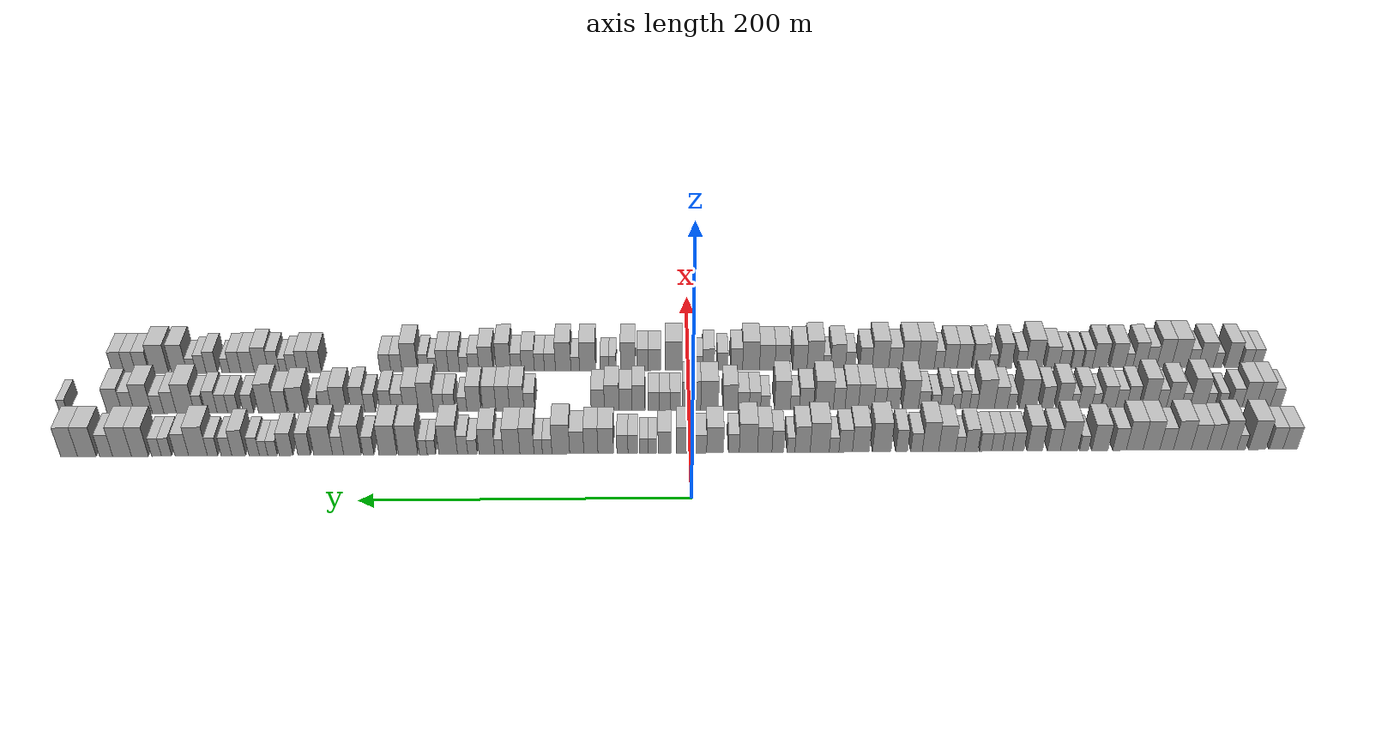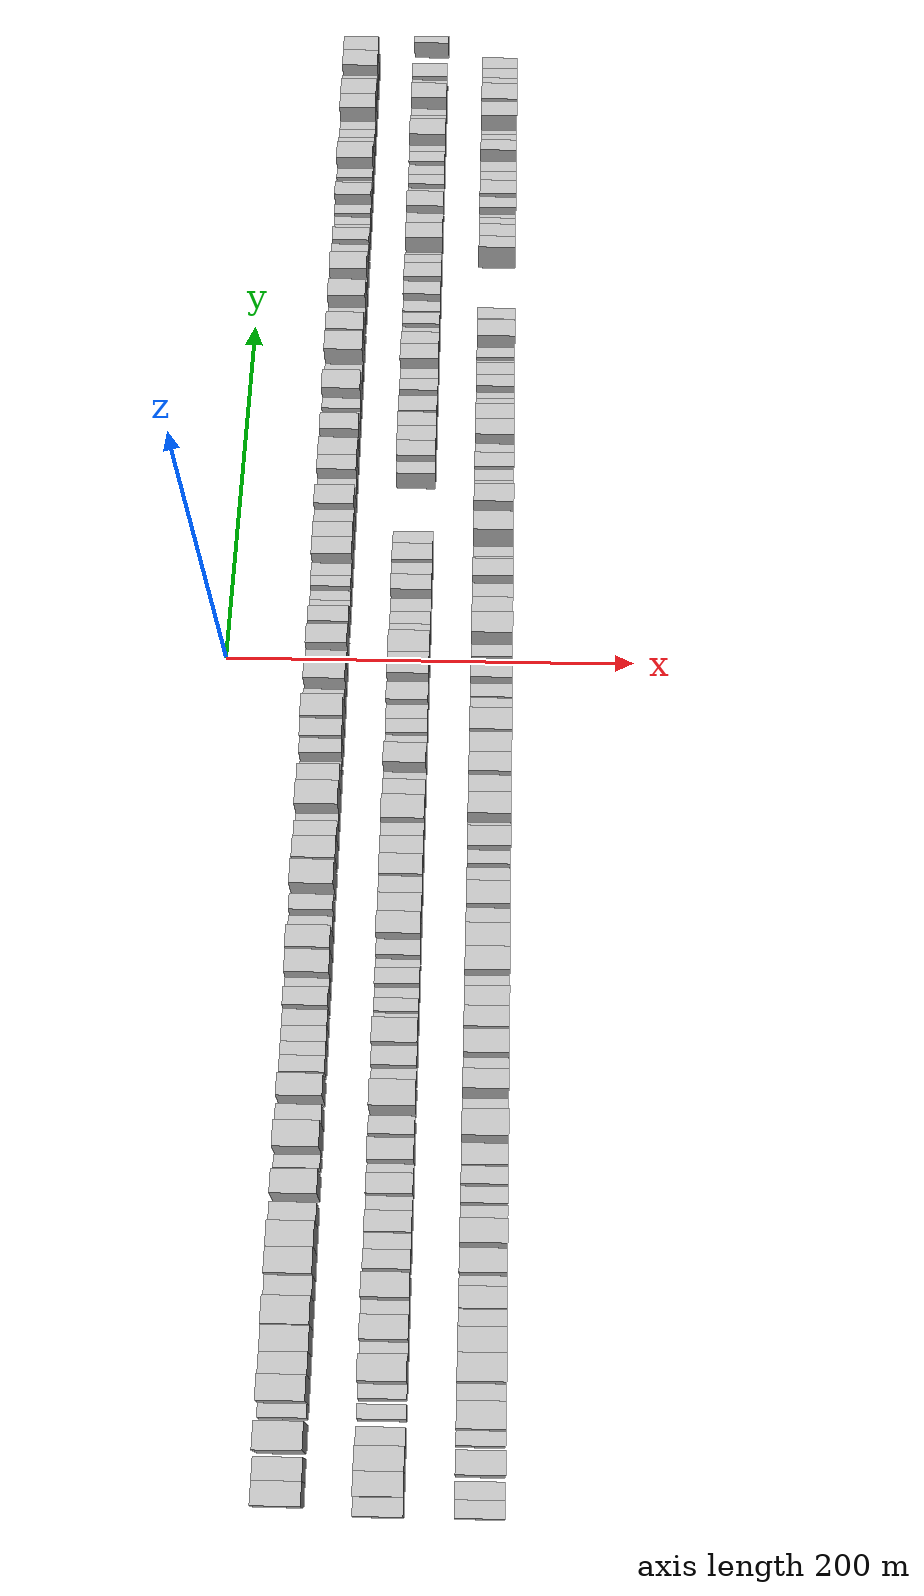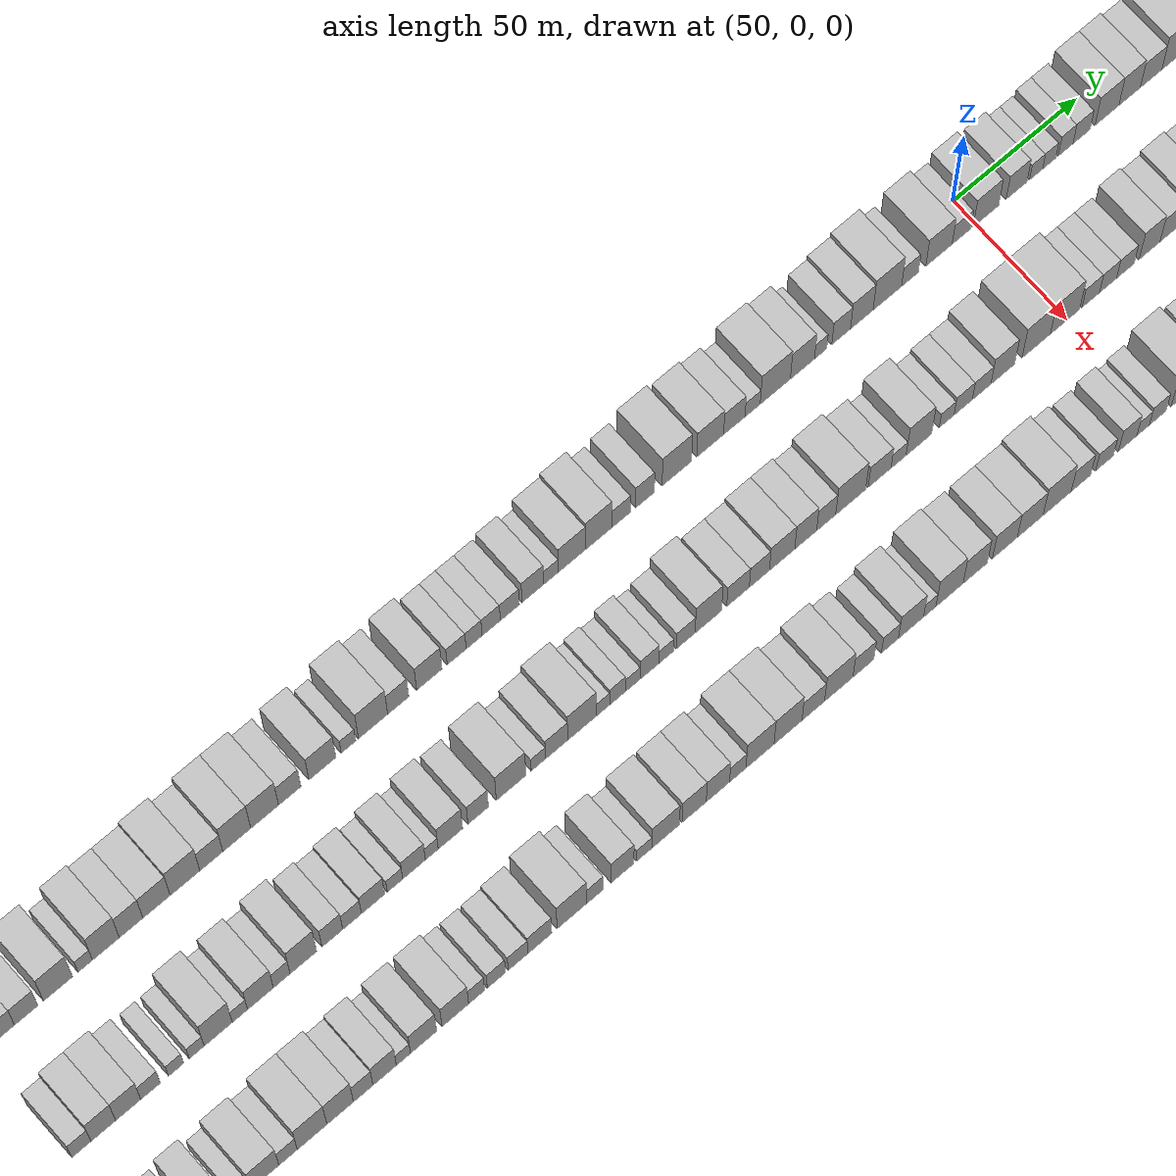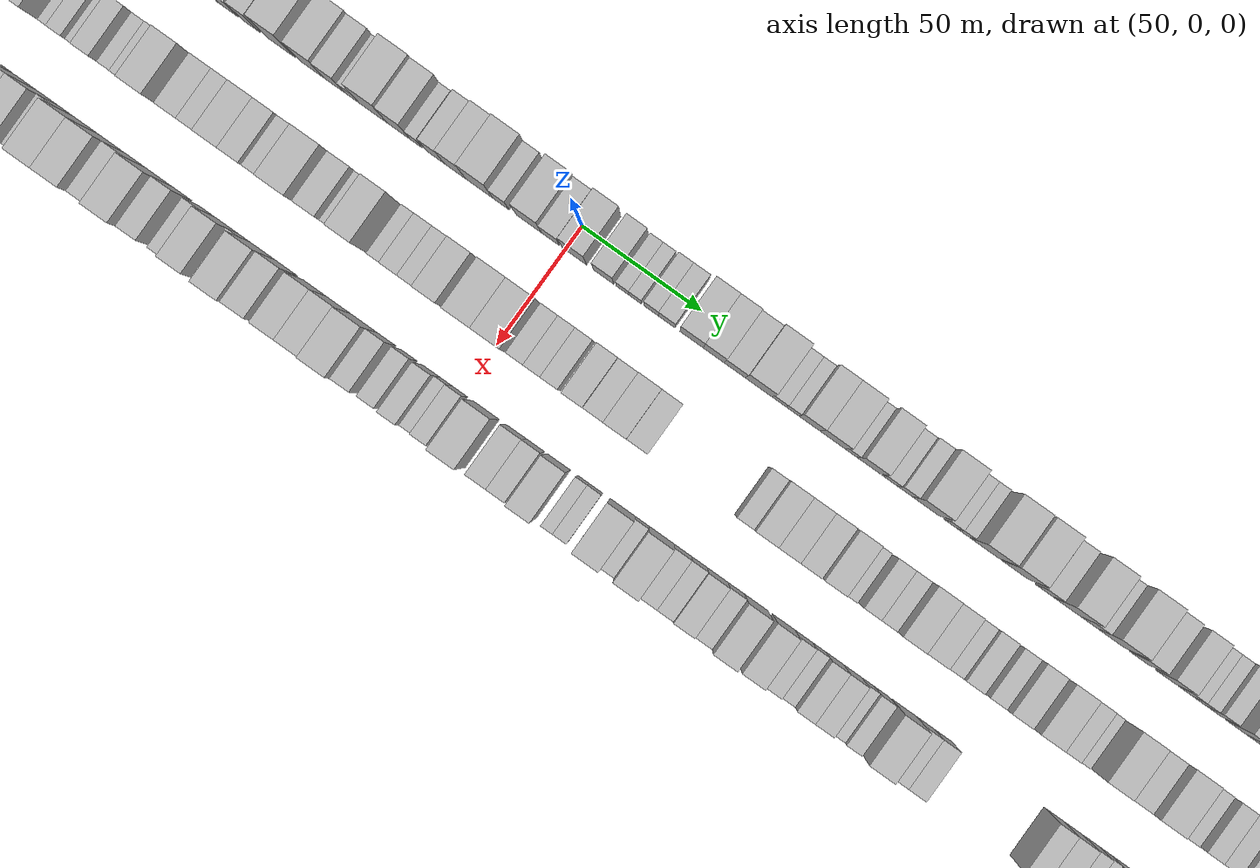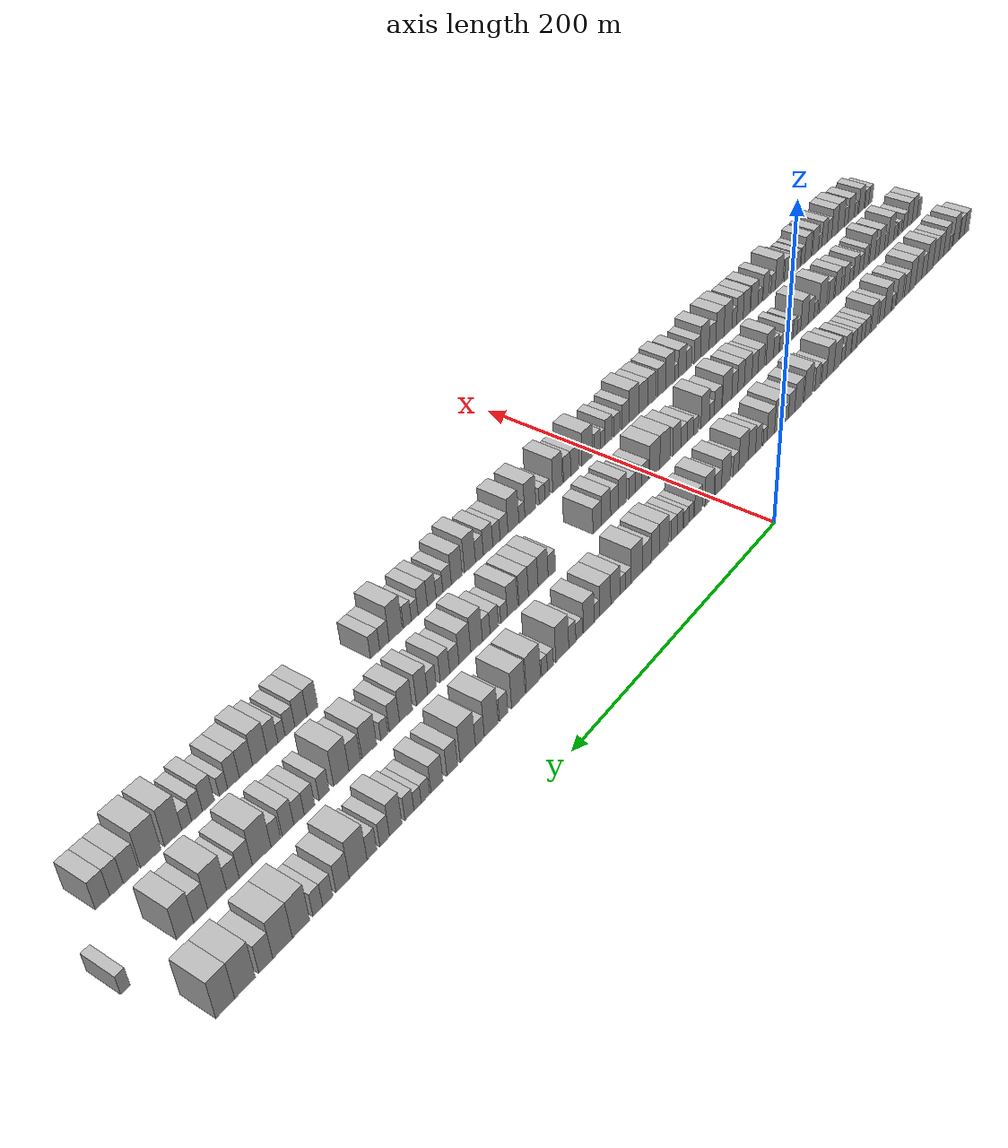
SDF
<sdf version="1.6">
 <world name="default">
  <scene>
   <sky><clouds><speed>12</speed></clouds></sky>
   <ambient>0.4 0.4 0.4 1</ambient>
   <background>0.7 0.7 0.7 1</background>
   <shadows>1</shadows>
  </scene>
  <gravity>0 0 -9.8066</gravity>
  <magnetic_field>6e-06 2.3e-05 -4.2e-05</magnetic_field>
  <physics default="0" name="default_physics" type="ode">
   <ode>
    <solver>
     <type>quick</type>
     <iters>10</iters>
     <sor>1.0</sor>
     <use_dynamic_moi_rescaling>0</use_dynamic_moi_rescaling>
    </solver>
    <constraints>
     <cfm>0</cfm>
     <erp>0.2</erp>
     <contact_max_correcting_vel>100</contact_max_correcting_vel>
     <contact_surface_layer>0.001</contact_surface_layer>
    </constraints>
   </ode>
   <max_step_size>0.004</max_step_size>
   <real_time_factor>1</real_time_factor>
   <real_time_update_rate>250</real_time_update_rate>
  </physics>
  <light name="sun" type="directional">
   <pose>0 0 10 0 0 0</pose>
   <diffuse>0.8 0.8 0.8 1</diffuse>
   <specular>0.2 0.2 0.2 1</specular>
   <attenuation>
    <range>1000</range>
    <constant>0.9</constant>
    <linear>0.01</linear>
    <quadratic>0.001</quadratic>
   </attenuation>
   <direction>-0.5 0.1 -0.9</direction>
  </light>
  <model name="building_1">
   <static>1</static>
   <pose>50.0000 -372.5119 0 0.000000 0.000000 0.000000</pose>
   <link name="link">
    <pose>0 0 9.00 0 0 0</pose>
    <collision name="collision"><geometry><box><size>20.0000 8.9763 18.0000</size></box></geometry></collision>
    <visual name="visual">
     <cast_shadows>0</cast_shadows>
     <geometry><box><size>20.0000 8.9763 18.0000</size></box></geometry>
     <material>
      <script>
       <uri>model://HANNAS_wall/materials/scripts</uri>
       <uri>model://HANNAS_wall/materials/textures</uri>
       <name>vrc/HANNAS_wall</name>
      </script>
     </material>
    </visual>
   </link>
  </model>
  <model name="building_2">
   <static>1</static>
   <pose>50.0000 -363.7410 0 0.000000 0.000000 0.000000</pose>
   <link name="link">
    <pose>0 0 9.00 0 0 0</pose>
    <collision name="collision"><geometry><box><size>20.0000 8.5655 18.0000</size></box></geometry></collision>
    <visual name="visual">
     <cast_shadows>0</cast_shadows>
     <geometry><box><size>20.0000 8.5655 18.0000</size></box></geometry>
     <material>
      <script>
       <uri>model://HANNAS_wall/materials/scripts</uri>
       <uri>model://HANNAS_wall/materials/textures</uri>
       <name>vrc/HANNAS_wall</name>
      </script>
     </material>
    </visual>
   </link>
  </model>
  <model name="building_3">
   <static>1</static>
   <pose>50.0000 -352.1159 0 0.000000 0.000000 0.000000</pose>
   <link name="link">
    <pose>0 0 12.00 0 0 0</pose>
    <collision name="collision"><geometry><box><size>20.0000 10.6847 24.0000</size></box></geometry></collision>
    <visual name="visual">
     <cast_shadows>0</cast_shadows>
     <geometry><box><size>20.0000 10.6847 24.0000</size></box></geometry>
     <material>
      <script>
       <uri>model://HANNAS_wall/materials/scripts</uri>
       <uri>model://HANNAS_wall/materials/textures</uri>
       <name>vrc/HANNAS_wall</name>
      </script>
     </material>
    </visual>
   </link>
  </model>
  <model name="building_4">
   <static>1</static>
   <pose>50.0000 -342.1169 0 0.000000 0.000000 0.000000</pose>
   <link name="link">
    <pose>0 0 6.00 0 0 0</pose>
    <collision name="collision"><geometry><box><size>20.0000 5.3132 12.0000</size></box></geometry></collision>
    <visual name="visual">
     <cast_shadows>0</cast_shadows>
     <geometry><box><size>20.0000 5.3132 12.0000</size></box></geometry>
     <material>
      <script>
       <uri>model://HANNAS_wall/materials/scripts</uri>
       <uri>model://HANNAS_wall/materials/textures</uri>
       <name>vrc/HANNAS_wall</name>
      </script>
     </material>
    </visual>
   </link>
  </model>
  <model name="building_5">
   <static>1</static>
   <pose>50.0000 -334.5347 0 0.000000 0.000000 0.000000</pose>
   <link name="link">
    <pose>0 0 12.00 0 0 0</pose>
    <collision name="collision"><geometry><box><size>20.0000 9.8513 24.0000</size></box></geometry></collision>
    <visual name="visual">
     <cast_shadows>0</cast_shadows>
     <geometry><box><size>20.0000 9.8513 24.0000</size></box></geometry>
     <material>
      <script>
       <uri>model://HANNAS_wall/materials/scripts</uri>
       <uri>model://HANNAS_wall/materials/textures</uri>
       <name>vrc/HANNAS_wall</name>
      </script>
     </material>
    </visual>
   </link>
  </model>
  <model name="building_6">
   <static>1</static>
   <pose>50.0000 -325.2550 0 0.000000 0.000000 0.000000</pose>
   <link name="link">
    <pose>0 0 10.50 0 0 0</pose>
    <collision name="collision"><geometry><box><size>20.0000 8.7081 21.0000</size></box></geometry></collision>
    <visual name="visual">
     <cast_shadows>0</cast_shadows>
     <geometry><box><size>20.0000 8.7081 21.0000</size></box></geometry>
     <material>
      <script>
       <uri>model://HANNAS_wall/materials/scripts</uri>
       <uri>model://HANNAS_wall/materials/textures</uri>
       <name>vrc/HANNAS_wall</name>
      </script>
     </material>
    </visual>
   </link>
  </model>
  <model name="building_7">
   <static>1</static>
   <pose>50.0000 -315.8533 0 0.000000 0.000000 0.000000</pose>
   <link name="link">
    <pose>0 0 10.50 0 0 0</pose>
    <collision name="collision"><geometry><box><size>20.0000 10.0951 21.0000</size></box></geometry></collision>
    <visual name="visual">
     <cast_shadows>0</cast_shadows>
     <geometry><box><size>20.0000 10.0951 21.0000</size></box></geometry>
     <material>
      <script>
       <uri>model://HANNAS_wall/materials/scripts</uri>
       <uri>model://HANNAS_wall/materials/textures</uri>
       <name>vrc/HANNAS_wall</name>
      </script>
     </material>
    </visual>
   </link>
  </model>
  <model name="building_8">
   <static>1</static>
   <pose>50.0000 -305.2932 0 0.000000 0.000000 0.000000</pose>
   <link name="link">
    <pose>0 0 12.00 0 0 0</pose>
    <collision name="collision"><geometry><box><size>20.0000 11.0251 24.0000</size></box></geometry></collision>
    <visual name="visual">
     <cast_shadows>0</cast_shadows>
     <geometry><box><size>20.0000 11.0251 24.0000</size></box></geometry>
     <material>
      <script>
       <uri>model://HANNAS_wall/materials/scripts</uri>
       <uri>model://HANNAS_wall/materials/textures</uri>
       <name>vrc/HANNAS_wall</name>
      </script>
     </material>
    </visual>
   </link>
  </model>
  <model name="building_9">
   <static>1</static>
   <pose>50.0000 -295.5040 0 0.000000 0.000000 0.000000</pose>
   <link name="link">
    <pose>0 0 9.00 0 0 0</pose>
    <collision name="collision"><geometry><box><size>20.0000 8.5534 18.0000</size></box></geometry></collision>
    <visual name="visual">
     <cast_shadows>0</cast_shadows>
     <geometry><box><size>20.0000 8.5534 18.0000</size></box></geometry>
     <material>
      <script>
       <uri>model://HANNAS_wall/materials/scripts</uri>
       <uri>model://HANNAS_wall/materials/textures</uri>
       <name>vrc/HANNAS_wall</name>
      </script>
     </material>
    </visual>
   </link>
  </model>
  <model name="building_10">
   <static>1</static>
   <pose>50.0000 -286.0187 0 0.000000 0.000000 0.000000</pose>
   <link name="link">
    <pose>0 0 12.00 0 0 0</pose>
    <collision name="collision"><geometry><box><size>20.0000 10.4171 24.0000</size></box></geometry></collision>
    <visual name="visual">
     <cast_shadows>0</cast_shadows>
     <geometry><box><size>20.0000 10.4171 24.0000</size></box></geometry>
     <material>
      <script>
       <uri>model://HANNAS_wall/materials/scripts</uri>
       <uri>model://HANNAS_wall/materials/textures</uri>
       <name>vrc/HANNAS_wall</name>
      </script>
     </material>
    </visual>
   </link>
  </model>
  <model name="building_11">
   <static>1</static>
   <pose>50.0000 -275.6110 0 0.000000 0.000000 0.000000</pose>
   <link name="link">
    <pose>0 0 12.00 0 0 0</pose>
    <collision name="collision"><geometry><box><size>20.0000 10.3982 24.0000</size></box></geometry></collision>
    <visual name="visual">
     <cast_shadows>0</cast_shadows>
     <geometry><box><size>20.0000 10.3982 24.0000</size></box></geometry>
     <material>
      <script>
       <uri>model://HANNAS_wall/materials/scripts</uri>
       <uri>model://HANNAS_wall/materials/textures</uri>
       <name>vrc/HANNAS_wall</name>
      </script>
     </material>
    </visual>
   </link>
  </model>
  <model name="building_12">
   <static>1</static>
   <pose>50.0000 -266.2202 0 0.000000 0.000000 0.000000</pose>
   <link name="link">
    <pose>0 0 9.00 0 0 0</pose>
    <collision name="collision"><geometry><box><size>20.0000 8.3834 18.0000</size></box></geometry></collision>
    <visual name="visual">
     <cast_shadows>0</cast_shadows>
     <geometry><box><size>20.0000 8.3834 18.0000</size></box></geometry>
     <material>
      <script>
       <uri>model://HANNAS_wall/materials/scripts</uri>
       <uri>model://HANNAS_wall/materials/textures</uri>
       <name>vrc/HANNAS_wall</name>
      </script>
     </material>
    </visual>
   </link>
  </model>
  <model name="building_13">
   <static>1</static>
   <pose>50.0000 -253.9671 0 0.000000 0.000000 0.000000</pose>
   <link name="link">
    <pose>0 0 10.50 0 0 0</pose>
    <collision name="collision"><geometry><box><size>20.0000 10.1227 21.0000</size></box></geometry></collision>
    <visual name="visual">
     <cast_shadows>0</cast_shadows>
     <geometry><box><size>20.0000 10.1227 21.0000</size></box></geometry>
     <material>
      <script>
       <uri>model://HANNAS_wall/materials/scripts</uri>
       <uri>model://HANNAS_wall/materials/textures</uri>
       <name>vrc/HANNAS_wall</name>
      </script>
     </material>
    </visual>
   </link>
  </model>
  <model name="building_14">
   <static>1</static>
   <pose>50.0000 -244.1444 0 0.000000 0.000000 0.000000</pose>
   <link name="link">
    <pose>0 0 6.00 0 0 0</pose>
    <collision name="collision"><geometry><box><size>20.0000 5.5228 12.0000</size></box></geometry></collision>
    <visual name="visual">
     <cast_shadows>0</cast_shadows>
     <geometry><box><size>20.0000 5.5228 12.0000</size></box></geometry>
     <material>
      <script>
       <uri>model://HANNAS_wall/materials/scripts</uri>
       <uri>model://HANNAS_wall/materials/textures</uri>
       <name>vrc/HANNAS_wall</name>
      </script>
     </material>
    </visual>
   </link>
  </model>
  <model name="building_15">
   <static>1</static>
   <pose>50.0000 -234.8598 0 0.000000 0.000000 0.000000</pose>
   <link name="link">
    <pose>0 0 12.00 0 0 0</pose>
    <collision name="collision"><geometry><box><size>20.0000 11.0464 24.0000</size></box></geometry></collision>
    <visual name="visual">
     <cast_shadows>0</cast_shadows>
     <geometry><box><size>20.0000 11.0464 24.0000</size></box></geometry>
     <material>
      <script>
       <uri>model://HANNAS_wall/materials/scripts</uri>
       <uri>model://HANNAS_wall/materials/textures</uri>
       <name>vrc/HANNAS_wall</name>
      </script>
     </material>
    </visual>
   </link>
  </model>
  <model name="building_16">
   <static>1</static>
   <pose>50.0000 -225.3460 0 0.000000 0.000000 0.000000</pose>
   <link name="link">
    <pose>0 0 9.00 0 0 0</pose>
    <collision name="collision"><geometry><box><size>20.0000 7.9812 18.0000</size></box></geometry></collision>
    <visual name="visual">
     <cast_shadows>0</cast_shadows>
     <geometry><box><size>20.0000 7.9812 18.0000</size></box></geometry>
     <material>
      <script>
       <uri>model://HANNAS_wall/materials/scripts</uri>
       <uri>model://HANNAS_wall/materials/textures</uri>
       <name>vrc/HANNAS_wall</name>
      </script>
     </material>
    </visual>
   </link>
  </model>
  <model name="building_17">
   <static>1</static>
   <pose>50.0000 -213.5502 0 0.000000 0.000000 0.000000</pose>
   <link name="link">
    <pose>0 0 10.50 0 0 0</pose>
    <collision name="collision"><geometry><box><size>20.0000 9.6105 21.0000</size></box></geometry></collision>
    <visual name="visual">
     <cast_shadows>0</cast_shadows>
     <geometry><box><size>20.0000 9.6105 21.0000</size></box></geometry>
     <material>
      <script>
       <uri>model://HANNAS_wall/materials/scripts</uri>
       <uri>model://HANNAS_wall/materials/textures</uri>
       <name>vrc/HANNAS_wall</name>
      </script>
     </material>
    </visual>
   </link>
  </model>
  <model name="building_18">
   <static>1</static>
   <pose>50.0000 -203.1293 0 0.000000 0.000000 0.000000</pose>
   <link name="link">
    <pose>0 0 7.50 0 0 0</pose>
    <collision name="collision"><geometry><box><size>20.0000 7.2313 15.0000</size></box></geometry></collision>
    <visual name="visual">
     <cast_shadows>0</cast_shadows>
     <geometry><box><size>20.0000 7.2313 15.0000</size></box></geometry>
     <material>
      <script>
       <uri>model://HANNAS_wall/materials/scripts</uri>
       <uri>model://HANNAS_wall/materials/textures</uri>
       <name>vrc/HANNAS_wall</name>
      </script>
     </material>
    </visual>
   </link>
  </model>
  <model name="building_19">
   <static>1</static>
   <pose>50.0000 -196.4776 0 0.000000 0.000000 0.000000</pose>
   <link name="link">
    <pose>0 0 7.50 0 0 0</pose>
    <collision name="collision"><geometry><box><size>20.0000 6.0720 15.0000</size></box></geometry></collision>
    <visual name="visual">
     <cast_shadows>0</cast_shadows>
     <geometry><box><size>20.0000 6.0720 15.0000</size></box></geometry>
     <material>
      <script>
       <uri>model://HANNAS_wall/materials/scripts</uri>
       <uri>model://HANNAS_wall/materials/textures</uri>
       <name>vrc/HANNAS_wall</name>
      </script>
     </material>
    </visual>
   </link>
  </model>
  <model name="building_20">
   <static>1</static>
   <pose>50.0000 -189.9568 0 0.000000 0.000000 0.000000</pose>
   <link name="link">
    <pose>0 0 7.50 0 0 0</pose>
    <collision name="collision"><geometry><box><size>20.0000 6.9697 15.0000</size></box></geometry></collision>
    <visual name="visual">
     <cast_shadows>0</cast_shadows>
     <geometry><box><size>20.0000 6.9697 15.0000</size></box></geometry>
     <material>
      <script>
       <uri>model://HANNAS_wall/materials/scripts</uri>
       <uri>model://HANNAS_wall/materials/textures</uri>
       <name>vrc/HANNAS_wall</name>
      </script>
     </material>
    </visual>
   </link>
  </model>
  <model name="building_21">
   <static>1</static>
   <pose>50.0000 -182.8175 0 0.000000 0.000000 0.000000</pose>
   <link name="link">
    <pose>0 0 7.50 0 0 0</pose>
    <collision name="collision"><geometry><box><size>20.0000 7.3088 15.0000</size></box></geometry></collision>
    <visual name="visual">
     <cast_shadows>0</cast_shadows>
     <geometry><box><size>20.0000 7.3088 15.0000</size></box></geometry>
     <material>
      <script>
       <uri>model://HANNAS_wall/materials/scripts</uri>
       <uri>model://HANNAS_wall/materials/textures</uri>
       <name>vrc/HANNAS_wall</name>
      </script>
     </material>
    </visual>
   </link>
  </model>
  <model name="building_22">
   <static>1</static>
   <pose>50.0000 -173.9836 0 0.000000 0.000000 0.000000</pose>
   <link name="link">
    <pose>0 0 9.00 0 0 0</pose>
    <collision name="collision"><geometry><box><size>20.0000 8.3590 18.0000</size></box></geometry></collision>
    <visual name="visual">
     <cast_shadows>0</cast_shadows>
     <geometry><box><size>20.0000 8.3590 18.0000</size></box></geometry>
     <material>
      <script>
       <uri>model://HANNAS_wall/materials/scripts</uri>
       <uri>model://HANNAS_wall/materials/textures</uri>
       <name>vrc/HANNAS_wall</name>
      </script>
     </material>
    </visual>
   </link>
  </model>
  <model name="building_23">
   <static>1</static>
   <pose>50.0000 -166.9671 0 0.000000 0.000000 0.000000</pose>
   <link name="link">
    <pose>0 0 6.00 0 0 0</pose>
    <collision name="collision"><geometry><box><size>20.0000 5.6740 12.0000</size></box></geometry></collision>
    <visual name="visual">
     <cast_shadows>0</cast_shadows>
     <geometry><box><size>20.0000 5.6740 12.0000</size></box></geometry>
     <material>
      <script>
       <uri>model://HANNAS_wall/materials/scripts</uri>
       <uri>model://HANNAS_wall/materials/textures</uri>
       <name>vrc/HANNAS_wall</name>
      </script>
     </material>
    </visual>
   </link>
  </model>
  <model name="building_24">
   <static>1</static>
   <pose>50.0000 -158.9029 0 0.000000 0.000000 0.000000</pose>
   <link name="link">
    <pose>0 0 10.50 0 0 0</pose>
    <collision name="collision"><geometry><box><size>20.0000 10.4545 21.0000</size></box></geometry></collision>
    <visual name="visual">
     <cast_shadows>0</cast_shadows>
     <geometry><box><size>20.0000 10.4545 21.0000</size></box></geometry>
     <material>
      <script>
       <uri>model://HANNAS_wall/materials/scripts</uri>
       <uri>model://HANNAS_wall/materials/textures</uri>
       <name>vrc/HANNAS_wall</name>
      </script>
     </material>
    </visual>
   </link>
  </model>
  <model name="building_25">
   <static>1</static>
   <pose>50.0000 -148.5779 0 0.000000 0.000000 0.000000</pose>
   <link name="link">
    <pose>0 0 12.00 0 0 0</pose>
    <collision name="collision"><geometry><box><size>20.0000 10.1955 24.0000</size></box></geometry></collision>
    <visual name="visual">
     <cast_shadows>0</cast_shadows>
     <geometry><box><size>20.0000 10.1955 24.0000</size></box></geometry>
     <material>
      <script>
       <uri>model://HANNAS_wall/materials/scripts</uri>
       <uri>model://HANNAS_wall/materials/textures</uri>
       <name>vrc/HANNAS_wall</name>
      </script>
     </material>
    </visual>
   </link>
  </model>
  <model name="building_26">
   <static>1</static>
   <pose>50.0000 -139.8926 0 0.000000 0.000000 0.000000</pose>
   <link name="link">
    <pose>0 0 7.50 0 0 0</pose>
    <collision name="collision"><geometry><box><size>20.0000 7.1751 15.0000</size></box></geometry></collision>
    <visual name="visual">
     <cast_shadows>0</cast_shadows>
     <geometry><box><size>20.0000 7.1751 15.0000</size></box></geometry>
     <material>
      <script>
       <uri>model://HANNAS_wall/materials/scripts</uri>
       <uri>model://HANNAS_wall/materials/textures</uri>
       <name>vrc/HANNAS_wall</name>
      </script>
     </material>
    </visual>
   </link>
  </model>
  <model name="building_27">
   <static>1</static>
   <pose>50.0000 -130.6790 0 0.000000 0.000000 0.000000</pose>
   <link name="link">
    <pose>0 0 9.00 0 0 0</pose>
    <collision name="collision"><geometry><box><size>20.0000 7.2520 18.0000</size></box></geometry></collision>
    <visual name="visual">
     <cast_shadows>0</cast_shadows>
     <geometry><box><size>20.0000 7.2520 18.0000</size></box></geometry>
     <material>
      <script>
       <uri>model://HANNAS_wall/materials/scripts</uri>
       <uri>model://HANNAS_wall/materials/textures</uri>
       <name>vrc/HANNAS_wall</name>
      </script>
     </material>
    </visual>
   </link>
  </model>
  <model name="building_28">
   <static>1</static>
   <pose>50.0000 -118.3185 0 0.000000 0.000000 0.000000</pose>
   <link name="link">
    <pose>0 0 12.00 0 0 0</pose>
    <collision name="collision"><geometry><box><size>20.0000 11.4691 24.0000</size></box></geometry></collision>
    <visual name="visual">
     <cast_shadows>0</cast_shadows>
     <geometry><box><size>20.0000 11.4691 24.0000</size></box></geometry>
     <material>
      <script>
       <uri>model://HANNAS_wall/materials/scripts</uri>
       <uri>model://HANNAS_wall/materials/textures</uri>
       <name>vrc/HANNAS_wall</name>
      </script>
     </material>
    </visual>
   </link>
  </model>
  <model name="building_29">
   <static>1</static>
   <pose>50.0000 -105.3368 0 0.000000 0.000000 0.000000</pose>
   <link name="link">
    <pose>0 0 10.50 0 0 0</pose>
    <collision name="collision"><geometry><box><size>20.0000 10.4943 21.0000</size></box></geometry></collision>
    <visual name="visual">
     <cast_shadows>0</cast_shadows>
     <geometry><box><size>20.0000 10.4943 21.0000</size></box></geometry>
     <material>
      <script>
       <uri>model://HANNAS_wall/materials/scripts</uri>
       <uri>model://HANNAS_wall/materials/textures</uri>
       <name>vrc/HANNAS_wall</name>
      </script>
     </material>
    </visual>
   </link>
  </model>
  <model name="building_30">
   <static>1</static>
   <pose>50.0000 -95.8908 0 0.000000 0.000000 0.000000</pose>
   <link name="link">
    <pose>0 0 9.00 0 0 0</pose>
    <collision name="collision"><geometry><box><size>20.0000 8.3976 18.0000</size></box></geometry></collision>
    <visual name="visual">
     <cast_shadows>0</cast_shadows>
     <geometry><box><size>20.0000 8.3976 18.0000</size></box></geometry>
     <material>
      <script>
       <uri>model://HANNAS_wall/materials/scripts</uri>
       <uri>model://HANNAS_wall/materials/textures</uri>
       <name>vrc/HANNAS_wall</name>
      </script>
     </material>
    </visual>
   </link>
  </model>
  <model name="building_31">
   <static>1</static>
   <pose>50.0000 -88.7096 0 0.000000 0.000000 0.000000</pose>
   <link name="link">
    <pose>0 0 6.00 0 0 0</pose>
    <collision name="collision"><geometry><box><size>20.0000 5.9648 12.0000</size></box></geometry></collision>
    <visual name="visual">
     <cast_shadows>0</cast_shadows>
     <geometry><box><size>20.0000 5.9648 12.0000</size></box></geometry>
     <material>
      <script>
       <uri>model://HANNAS_wall/materials/scripts</uri>
       <uri>model://HANNAS_wall/materials/textures</uri>
       <name>vrc/HANNAS_wall</name>
      </script>
     </material>
    </visual>
   </link>
  </model>
  <model name="building_32">
   <static>1</static>
   <pose>50.0000 -79.7945 0 0.000000 0.000000 0.000000</pose>
   <link name="link">
    <pose>0 0 12.00 0 0 0</pose>
    <collision name="collision"><geometry><box><size>20.0000 11.8655 24.0000</size></box></geometry></collision>
    <visual name="visual">
     <cast_shadows>0</cast_shadows>
     <geometry><box><size>20.0000 11.8655 24.0000</size></box></geometry>
     <material>
      <script>
       <uri>model://HANNAS_wall/materials/scripts</uri>
       <uri>model://HANNAS_wall/materials/textures</uri>
       <name>vrc/HANNAS_wall</name>
      </script>
     </material>
    </visual>
   </link>
  </model>
  <model name="building_33">
   <static>1</static>
   <pose>50.0000 -69.1107 0 0.000000 0.000000 0.000000</pose>
   <link name="link">
    <pose>0 0 10.50 0 0 0</pose>
    <collision name="collision"><geometry><box><size>20.0000 9.5022 21.0000</size></box></geometry></collision>
    <visual name="visual">
     <cast_shadows>0</cast_shadows>
     <geometry><box><size>20.0000 9.5022 21.0000</size></box></geometry>
     <material>
      <script>
       <uri>model://HANNAS_wall/materials/scripts</uri>
       <uri>model://HANNAS_wall/materials/textures</uri>
       <name>vrc/HANNAS_wall</name>
      </script>
     </material>
    </visual>
   </link>
  </model>
  <model name="building_34">
   <static>1</static>
   <pose>50.0000 -61.9324 0 0.000000 0.000000 0.000000</pose>
   <link name="link">
    <pose>0 0 6.00 0 0 0</pose>
    <collision name="collision"><geometry><box><size>20.0000 4.8543 12.0000</size></box></geometry></collision>
    <visual name="visual">
     <cast_shadows>0</cast_shadows>
     <geometry><box><size>20.0000 4.8543 12.0000</size></box></geometry>
     <material>
      <script>
       <uri>model://HANNAS_wall/materials/scripts</uri>
       <uri>model://HANNAS_wall/materials/textures</uri>
       <name>vrc/HANNAS_wall</name>
      </script>
     </material>
    </visual>
   </link>
  </model>
  <model name="building_35">
   <static>1</static>
   <pose>50.0000 -53.8134 0 0.000000 0.000000 0.000000</pose>
   <link name="link">
    <pose>0 0 9.00 0 0 0</pose>
    <collision name="collision"><geometry><box><size>20.0000 7.3838 18.0000</size></box></geometry></collision>
    <visual name="visual">
     <cast_shadows>0</cast_shadows>
     <geometry><box><size>20.0000 7.3838 18.0000</size></box></geometry>
     <material>
      <script>
       <uri>model://HANNAS_wall/materials/scripts</uri>
       <uri>model://HANNAS_wall/materials/textures</uri>
       <name>vrc/HANNAS_wall</name>
      </script>
     </material>
    </visual>
   </link>
  </model>
  <model name="building_36">
   <static>1</static>
   <pose>50.0000 -45.6521 0 0.000000 0.000000 0.000000</pose>
   <link name="link">
    <pose>0 0 10.50 0 0 0</pose>
    <collision name="collision"><geometry><box><size>20.0000 8.9389 21.0000</size></box></geometry></collision>
    <visual name="visual">
     <cast_shadows>0</cast_shadows>
     <geometry><box><size>20.0000 8.9389 21.0000</size></box></geometry>
     <material>
      <script>
       <uri>model://HANNAS_wall/materials/scripts</uri>
       <uri>model://HANNAS_wall/materials/textures</uri>
       <name>vrc/HANNAS_wall</name>
      </script>
     </material>
    </visual>
   </link>
  </model>
  <model name="building_37">
   <static>1</static>
   <pose>50.0000 -35.5213 0 0.000000 0.000000 0.000000</pose>
   <link name="link">
    <pose>0 0 12.00 0 0 0</pose>
    <collision name="collision"><geometry><box><size>20.0000 11.3226 24.0000</size></box></geometry></collision>
    <visual name="visual">
     <cast_shadows>0</cast_shadows>
     <geometry><box><size>20.0000 11.3226 24.0000</size></box></geometry>
     <material>
      <script>
       <uri>model://HANNAS_wall/materials/scripts</uri>
       <uri>model://HANNAS_wall/materials/textures</uri>
       <name>vrc/HANNAS_wall</name>
      </script>
     </material>
    </visual>
   </link>
  </model>
  <model name="building_38">
   <static>1</static>
   <pose>50.0000 -26.5018 0 0.000000 0.000000 0.000000</pose>
   <link name="link">
    <pose>0 0 7.50 0 0 0</pose>
    <collision name="collision"><geometry><box><size>20.0000 6.7164 15.0000</size></box></geometry></collision>
    <visual name="visual">
     <cast_shadows>0</cast_shadows>
     <geometry><box><size>20.0000 6.7164 15.0000</size></box></geometry>
     <material>
      <script>
       <uri>model://HANNAS_wall/materials/scripts</uri>
       <uri>model://HANNAS_wall/materials/textures</uri>
       <name>vrc/HANNAS_wall</name>
      </script>
     </material>
    </visual>
   </link>
  </model>
  <model name="building_39">
   <static>1</static>
   <pose>50.0000 -14.8969 0 0.000000 0.000000 0.000000</pose>
   <link name="link">
    <pose>0 0 10.50 0 0 0</pose>
    <collision name="collision"><geometry><box><size>20.0000 10.4936 21.0000</size></box></geometry></collision>
    <visual name="visual">
     <cast_shadows>0</cast_shadows>
     <geometry><box><size>20.0000 10.4936 21.0000</size></box></geometry>
     <material>
      <script>
       <uri>model://HANNAS_wall/materials/scripts</uri>
       <uri>model://HANNAS_wall/materials/textures</uri>
       <name>vrc/HANNAS_wall</name>
      </script>
     </material>
    </visual>
   </link>
  </model>
  <model name="building_40">
   <static>1</static>
   <pose>50.0000 -5.9136 0 0.000000 0.000000 0.000000</pose>
   <link name="link">
    <pose>0 0 7.50 0 0 0</pose>
    <collision name="collision"><geometry><box><size>20.0000 7.4729 15.0000</size></box></geometry></collision>
    <visual name="visual">
     <cast_shadows>0</cast_shadows>
     <geometry><box><size>20.0000 7.4729 15.0000</size></box></geometry>
     <material>
      <script>
       <uri>model://HANNAS_wall/materials/scripts</uri>
       <uri>model://HANNAS_wall/materials/textures</uri>
       <name>vrc/HANNAS_wall</name>
      </script>
     </material>
    </visual>
   </link>
  </model>
  <model name="building_41">
   <static>1</static>
   <pose>50.0000 3.9553 0 0.000000 0.000000 0.000000</pose>
   <link name="link">
    <pose>0 0 10.50 0 0 0</pose>
    <collision name="collision"><geometry><box><size>20.0000 10.2650 21.0000</size></box></geometry></collision>
    <visual name="visual">
     <cast_shadows>0</cast_shadows>
     <geometry><box><size>20.0000 10.2650 21.0000</size></box></geometry>
     <material>
      <script>
       <uri>model://HANNAS_wall/materials/scripts</uri>
       <uri>model://HANNAS_wall/materials/textures</uri>
       <name>vrc/HANNAS_wall</name>
      </script>
     </material>
    </visual>
   </link>
  </model>
  <model name="building_42">
   <static>1</static>
   <pose>50.0000 16.2901 0 0.000000 0.000000 0.000000</pose>
   <link name="link">
    <pose>0 0 9.00 0 0 0</pose>
    <collision name="collision"><geometry><box><size>20.0000 8.4046 18.0000</size></box></geometry></collision>
    <visual name="visual">
     <cast_shadows>0</cast_shadows>
     <geometry><box><size>20.0000 8.4046 18.0000</size></box></geometry>
     <material>
      <script>
       <uri>model://HANNAS_wall/materials/scripts</uri>
       <uri>model://HANNAS_wall/materials/textures</uri>
       <name>vrc/HANNAS_wall</name>
      </script>
     </material>
    </visual>
   </link>
  </model>
  <model name="building_43">
   <static>1</static>
   <pose>50.0000 24.1484 0 0.000000 0.000000 0.000000</pose>
   <link name="link">
    <pose>0 0 6.00 0 0 0</pose>
    <collision name="collision"><geometry><box><size>20.0000 5.3120 12.0000</size></box></geometry></collision>
    <visual name="visual">
     <cast_shadows>0</cast_shadows>
     <geometry><box><size>20.0000 5.3120 12.0000</size></box></geometry>
     <material>
      <script>
       <uri>model://HANNAS_wall/materials/scripts</uri>
       <uri>model://HANNAS_wall/materials/textures</uri>
       <name>vrc/HANNAS_wall</name>
      </script>
     </material>
    </visual>
   </link>
  </model>
  <model name="building_44">
   <static>1</static>
   <pose>50.0000 29.4460 0 0.000000 0.000000 0.000000</pose>
   <link name="link">
    <pose>0 0 6.00 0 0 0</pose>
    <collision name="collision"><geometry><box><size>20.0000 5.2832 12.0000</size></box></geometry></collision>
    <visual name="visual">
     <cast_shadows>0</cast_shadows>
     <geometry><box><size>20.0000 5.2832 12.0000</size></box></geometry>
     <material>
      <script>
       <uri>model://HANNAS_wall/materials/scripts</uri>
       <uri>model://HANNAS_wall/materials/textures</uri>
       <name>vrc/HANNAS_wall</name>
      </script>
     </material>
    </visual>
   </link>
  </model>
  <model name="building_45">
   <static>1</static>
   <pose>50.0000 36.1066 0 0.000000 0.000000 0.000000</pose>
   <link name="link">
    <pose>0 0 7.50 0 0 0</pose>
    <collision name="collision"><geometry><box><size>20.0000 6.0381 15.0000</size></box></geometry></collision>
    <visual name="visual">
     <cast_shadows>0</cast_shadows>
     <geometry><box><size>20.0000 6.0381 15.0000</size></box></geometry>
     <material>
      <script>
       <uri>model://HANNAS_wall/materials/scripts</uri>
       <uri>model://HANNAS_wall/materials/textures</uri>
       <name>vrc/HANNAS_wall</name>
      </script>
     </material>
    </visual>
   </link>
  </model>
  <model name="building_46">
   <static>1</static>
   <pose>50.0000 42.5712 0 0.000000 0.000000 0.000000</pose>
   <link name="link">
    <pose>0 0 7.50 0 0 0</pose>
    <collision name="collision"><geometry><box><size>20.0000 6.8910 15.0000</size></box></geometry></collision>
    <visual name="visual">
     <cast_shadows>0</cast_shadows>
     <geometry><box><size>20.0000 6.8910 15.0000</size></box></geometry>
     <material>
      <script>
       <uri>model://HANNAS_wall/materials/scripts</uri>
       <uri>model://HANNAS_wall/materials/textures</uri>
       <name>vrc/HANNAS_wall</name>
      </script>
     </material>
    </visual>
   </link>
  </model>
  <model name="building_47">
   <static>1</static>
   <pose>50.0000 52.8749 0 0.000000 0.000000 0.000000</pose>
   <link name="link">
    <pose>0 0 10.50 0 0 0</pose>
    <collision name="collision"><geometry><box><size>20.0000 9.7164 21.0000</size></box></geometry></collision>
    <visual name="visual">
     <cast_shadows>0</cast_shadows>
     <geometry><box><size>20.0000 9.7164 21.0000</size></box></geometry>
     <material>
      <script>
       <uri>model://HANNAS_wall/materials/scripts</uri>
       <uri>model://HANNAS_wall/materials/textures</uri>
       <name>vrc/HANNAS_wall</name>
      </script>
     </material>
    </visual>
   </link>
  </model>
  <model name="building_48">
   <static>1</static>
   <pose>50.0000 62.1032 0 0.000000 0.000000 0.000000</pose>
   <link name="link">
    <pose>0 0 10.50 0 0 0</pose>
    <collision name="collision"><geometry><box><size>20.0000 8.7401 21.0000</size></box></geometry></collision>
    <visual name="visual">
     <cast_shadows>0</cast_shadows>
     <geometry><box><size>20.0000 8.7401 21.0000</size></box></geometry>
     <material>
      <script>
       <uri>model://HANNAS_wall/materials/scripts</uri>
       <uri>model://HANNAS_wall/materials/textures</uri>
       <name>vrc/HANNAS_wall</name>
      </script>
     </material>
    </visual>
   </link>
  </model>
  <model name="building_49">
   <static>1</static>
   <pose>50.0000 70.8600 0 0.000000 0.000000 0.000000</pose>
   <link name="link">
    <pose>0 0 9.00 0 0 0</pose>
    <collision name="collision"><geometry><box><size>20.0000 8.7737 18.0000</size></box></geometry></collision>
    <visual name="visual">
     <cast_shadows>0</cast_shadows>
     <geometry><box><size>20.0000 8.7737 18.0000</size></box></geometry>
     <material>
      <script>
       <uri>model://HANNAS_wall/materials/scripts</uri>
       <uri>model://HANNAS_wall/materials/textures</uri>
       <name>vrc/HANNAS_wall</name>
      </script>
     </material>
    </visual>
   </link>
  </model>
  <model name="building_50">
   <static>1</static>
   <pose>50.0000 80.7420 0 0.000000 0.000000 0.000000</pose>
   <link name="link">
    <pose>0 0 12.00 0 0 0</pose>
    <collision name="collision"><geometry><box><size>20.0000 10.9903 24.0000</size></box></geometry></collision>
    <visual name="visual">
     <cast_shadows>0</cast_shadows>
     <geometry><box><size>20.0000 10.9903 24.0000</size></box></geometry>
     <material>
      <script>
       <uri>model://HANNAS_wall/materials/scripts</uri>
       <uri>model://HANNAS_wall/materials/textures</uri>
       <name>vrc/HANNAS_wall</name>
      </script>
     </material>
    </visual>
   </link>
  </model>
  <model name="building_51">
   <static>1</static>
   <pose>50.0000 89.1865 0 0.000000 0.000000 0.000000</pose>
   <link name="link">
    <pose>0 0 6.00 0 0 0</pose>
    <collision name="collision"><geometry><box><size>20.0000 5.8988 12.0000</size></box></geometry></collision>
    <visual name="visual">
     <cast_shadows>0</cast_shadows>
     <geometry><box><size>20.0000 5.8988 12.0000</size></box></geometry>
     <material>
      <script>
       <uri>model://HANNAS_wall/materials/scripts</uri>
       <uri>model://HANNAS_wall/materials/textures</uri>
       <name>vrc/HANNAS_wall</name>
      </script>
     </material>
    </visual>
   </link>
  </model>
  <model name="building_52">
   <static>1</static>
   <pose>50.0000 94.7149 0 0.000000 0.000000 0.000000</pose>
   <link name="link">
    <pose>0 0 6.00 0 0 0</pose>
    <collision name="collision"><geometry><box><size>20.0000 5.1579 12.0000</size></box></geometry></collision>
    <visual name="visual">
     <cast_shadows>0</cast_shadows>
     <geometry><box><size>20.0000 5.1579 12.0000</size></box></geometry>
     <material>
      <script>
       <uri>model://HANNAS_wall/materials/scripts</uri>
       <uri>model://HANNAS_wall/materials/textures</uri>
       <name>vrc/HANNAS_wall</name>
      </script>
     </material>
    </visual>
   </link>
  </model>
  <model name="building_53">
   <static>1</static>
   <pose>50.0000 101.6818 0 0.000000 0.000000 0.000000</pose>
   <link name="link">
    <pose>0 0 10.50 0 0 0</pose>
    <collision name="collision"><geometry><box><size>20.0000 8.7760 21.0000</size></box></geometry></collision>
    <visual name="visual">
     <cast_shadows>0</cast_shadows>
     <geometry><box><size>20.0000 8.7760 21.0000</size></box></geometry>
     <material>
      <script>
       <uri>model://HANNAS_wall/materials/scripts</uri>
       <uri>model://HANNAS_wall/materials/textures</uri>
       <name>vrc/HANNAS_wall</name>
      </script>
     </material>
    </visual>
   </link>
  </model>
  <model name="building_54">
   <static>1</static>
   <pose>50.0000 111.2973 0 0.000000 0.000000 0.000000</pose>
   <link name="link">
    <pose>0 0 10.50 0 0 0</pose>
    <collision name="collision"><geometry><box><size>20.0000 10.4549 21.0000</size></box></geometry></collision>
    <visual name="visual">
     <cast_shadows>0</cast_shadows>
     <geometry><box><size>20.0000 10.4549 21.0000</size></box></geometry>
     <material>
      <script>
       <uri>model://HANNAS_wall/materials/scripts</uri>
       <uri>model://HANNAS_wall/materials/textures</uri>
       <name>vrc/HANNAS_wall</name>
      </script>
     </material>
    </visual>
   </link>
  </model>
  <model name="building_55">
   <static>1</static>
   <pose>50.0000 119.0371 0 0.000000 0.000000 0.000000</pose>
   <link name="link">
    <pose>0 0 6.00 0 0 0</pose>
    <collision name="collision"><geometry><box><size>20.0000 5.0247 12.0000</size></box></geometry></collision>
    <visual name="visual">
     <cast_shadows>0</cast_shadows>
     <geometry><box><size>20.0000 5.0247 12.0000</size></box></geometry>
     <material>
      <script>
       <uri>model://HANNAS_wall/materials/scripts</uri>
       <uri>model://HANNAS_wall/materials/textures</uri>
       <name>vrc/HANNAS_wall</name>
      </script>
     </material>
    </visual>
   </link>
  </model>
  <model name="building_56">
   <static>1</static>
   <pose>50.0000 126.4788 0 0.000000 0.000000 0.000000</pose>
   <link name="link">
    <pose>0 0 10.50 0 0 0</pose>
    <collision name="collision"><geometry><box><size>20.0000 9.8587 21.0000</size></box></geometry></collision>
    <visual name="visual">
     <cast_shadows>0</cast_shadows>
     <geometry><box><size>20.0000 9.8587 21.0000</size></box></geometry>
     <material>
      <script>
       <uri>model://HANNAS_wall/materials/scripts</uri>
       <uri>model://HANNAS_wall/materials/textures</uri>
       <name>vrc/HANNAS_wall</name>
      </script>
     </material>
    </visual>
   </link>
  </model>
  <model name="building_57">
   <static>1</static>
   <pose>50.0000 135.3654 0 0.000000 0.000000 0.000000</pose>
   <link name="link">
    <pose>0 0 6.00 0 0 0</pose>
    <collision name="collision"><geometry><box><size>20.0000 5.9146 12.0000</size></box></geometry></collision>
    <visual name="visual">
     <cast_shadows>0</cast_shadows>
     <geometry><box><size>20.0000 5.9146 12.0000</size></box></geometry>
     <material>
      <script>
       <uri>model://HANNAS_wall/materials/scripts</uri>
       <uri>model://HANNAS_wall/materials/textures</uri>
       <name>vrc/HANNAS_wall</name>
      </script>
     </material>
    </visual>
   </link>
  </model>
  <model name="building_58">
   <static>1</static>
   <pose>50.0000 141.5063 0 0.000000 0.000000 0.000000</pose>
   <link name="link">
    <pose>0 0 7.50 0 0 0</pose>
    <collision name="collision"><geometry><box><size>20.0000 6.3672 15.0000</size></box></geometry></collision>
    <visual name="visual">
     <cast_shadows>0</cast_shadows>
     <geometry><box><size>20.0000 6.3672 15.0000</size></box></geometry>
     <material>
      <script>
       <uri>model://HANNAS_wall/materials/scripts</uri>
       <uri>model://HANNAS_wall/materials/textures</uri>
       <name>vrc/HANNAS_wall</name>
      </script>
     </material>
    </visual>
   </link>
  </model>
  <model name="building_59">
   <static>1</static>
   <pose>50.0000 150.4168 0 0.000000 0.000000 0.000000</pose>
   <link name="link">
    <pose>0 0 12.00 0 0 0</pose>
    <collision name="collision"><geometry><box><size>20.0000 11.4538 24.0000</size></box></geometry></collision>
    <visual name="visual">
     <cast_shadows>0</cast_shadows>
     <geometry><box><size>20.0000 11.4538 24.0000</size></box></geometry>
     <material>
      <script>
       <uri>model://HANNAS_wall/materials/scripts</uri>
       <uri>model://HANNAS_wall/materials/textures</uri>
       <name>vrc/HANNAS_wall</name>
      </script>
     </material>
    </visual>
   </link>
  </model>
  <model name="building_60">
   <static>1</static>
   <pose>50.0000 160.7680 0 0.000000 0.000000 0.000000</pose>
   <link name="link">
    <pose>0 0 6.00 0 0 0</pose>
    <collision name="collision"><geometry><box><size>20.0000 5.2487 12.0000</size></box></geometry></collision>
    <visual name="visual">
     <cast_shadows>0</cast_shadows>
     <geometry><box><size>20.0000 5.2487 12.0000</size></box></geometry>
     <material>
      <script>
       <uri>model://HANNAS_wall/materials/scripts</uri>
       <uri>model://HANNAS_wall/materials/textures</uri>
       <name>vrc/HANNAS_wall</name>
      </script>
     </material>
    </visual>
   </link>
  </model>
  <model name="building_61">
   <static>1</static>
   <pose>50.0000 165.8168 0 0.000000 0.000000 0.000000</pose>
   <link name="link">
    <pose>0 0 6.00 0 0 0</pose>
    <collision name="collision"><geometry><box><size>20.0000 4.8489 12.0000</size></box></geometry></collision>
    <visual name="visual">
     <cast_shadows>0</cast_shadows>
     <geometry><box><size>20.0000 4.8489 12.0000</size></box></geometry>
     <material>
      <script>
       <uri>model://HANNAS_wall/materials/scripts</uri>
       <uri>model://HANNAS_wall/materials/textures</uri>
       <name>vrc/HANNAS_wall</name>
      </script>
     </material>
    </visual>
   </link>
  </model>
  <model name="building_62">
   <static>1</static>
   <pose>50.0000 175.2082 0 0.000000 0.000000 0.000000</pose>
   <link name="link">
    <pose>0 0 12.00 0 0 0</pose>
    <collision name="collision"><geometry><box><size>20.0000 11.9339 24.0000</size></box></geometry></collision>
    <visual name="visual">
     <cast_shadows>0</cast_shadows>
     <geometry><box><size>20.0000 11.9339 24.0000</size></box></geometry>
     <material>
      <script>
       <uri>model://HANNAS_wall/materials/scripts</uri>
       <uri>model://HANNAS_wall/materials/textures</uri>
       <name>vrc/HANNAS_wall</name>
      </script>
     </material>
    </visual>
   </link>
  </model>
  <model name="building_63">
   <static>1</static>
   <pose>50.0000 187.7218 0 0.000000 0.000000 0.000000</pose>
   <link name="link">
    <pose>0 0 12.00 0 0 0</pose>
    <collision name="collision"><geometry><box><size>20.0000 11.0932 24.0000</size></box></geometry></collision>
    <visual name="visual">
     <cast_shadows>0</cast_shadows>
     <geometry><box><size>20.0000 11.0932 24.0000</size></box></geometry>
     <material>
      <script>
       <uri>model://HANNAS_wall/materials/scripts</uri>
       <uri>model://HANNAS_wall/materials/textures</uri>
       <name>vrc/HANNAS_wall</name>
      </script>
     </material>
    </visual>
   </link>
  </model>
  <model name="building_64">
   <static>1</static>
   <pose>50.0000 199.6790 0 0.000000 0.000000 0.000000</pose>
   <link name="link">
    <pose>0 0 7.50 0 0 0</pose>
    <collision name="collision"><geometry><box><size>20.0000 6.8211 15.0000</size></box></geometry></collision>
    <visual name="visual">
     <cast_shadows>0</cast_shadows>
     <geometry><box><size>20.0000 6.8211 15.0000</size></box></geometry>
     <material>
      <script>
       <uri>model://HANNAS_wall/materials/scripts</uri>
       <uri>model://HANNAS_wall/materials/textures</uri>
       <name>vrc/HANNAS_wall</name>
      </script>
     </material>
    </visual>
   </link>
  </model>
  <model name="building_65">
   <static>1</static>
   <pose>50.0000 209.5486 0 0.000000 0.000000 0.000000</pose>
   <link name="link">
    <pose>0 0 12.00 0 0 0</pose>
    <collision name="collision"><geometry><box><size>20.0000 10.9182 24.0000</size></box></geometry></collision>
    <visual name="visual">
     <cast_shadows>0</cast_shadows>
     <geometry><box><size>20.0000 10.9182 24.0000</size></box></geometry>
     <material>
      <script>
       <uri>model://HANNAS_wall/materials/scripts</uri>
       <uri>model://HANNAS_wall/materials/textures</uri>
       <name>vrc/HANNAS_wall</name>
      </script>
     </material>
    </visual>
   </link>
  </model>
  <model name="building_66">
   <static>1</static>
   <pose>50.0000 218.4576 0 0.000000 0.000000 0.000000</pose>
   <link name="link">
    <pose>0 0 7.50 0 0 0</pose>
    <collision name="collision"><geometry><box><size>20.0000 6.8998 15.0000</size></box></geometry></collision>
    <visual name="visual">
     <cast_shadows>0</cast_shadows>
     <geometry><box><size>20.0000 6.8998 15.0000</size></box></geometry>
     <material>
      <script>
       <uri>model://HANNAS_wall/materials/scripts</uri>
       <uri>model://HANNAS_wall/materials/textures</uri>
       <name>vrc/HANNAS_wall</name>
      </script>
     </material>
    </visual>
   </link>
  </model>
  <model name="building_67">
   <static>1</static>
   <pose>50.0000 227.6946 0 0.000000 0.000000 0.000000</pose>
   <link name="link">
    <pose>0 0 12.00 0 0 0</pose>
    <collision name="collision"><geometry><box><size>20.0000 11.5742 24.0000</size></box></geometry></collision>
    <visual name="visual">
     <cast_shadows>0</cast_shadows>
     <geometry><box><size>20.0000 11.5742 24.0000</size></box></geometry>
     <material>
      <script>
       <uri>model://HANNAS_wall/materials/scripts</uri>
       <uri>model://HANNAS_wall/materials/textures</uri>
       <name>vrc/HANNAS_wall</name>
      </script>
     </material>
    </visual>
   </link>
  </model>
  <model name="building_68">
   <static>1</static>
   <pose>50.0000 239.4182 0 0.000000 0.000000 0.000000</pose>
   <link name="link">
    <pose>0 0 9.00 0 0 0</pose>
    <collision name="collision"><geometry><box><size>20.0000 7.8730 18.0000</size></box></geometry></collision>
    <visual name="visual">
     <cast_shadows>0</cast_shadows>
     <geometry><box><size>20.0000 7.8730 18.0000</size></box></geometry>
     <material>
      <script>
       <uri>model://HANNAS_wall/materials/scripts</uri>
       <uri>model://HANNAS_wall/materials/textures</uri>
       <name>vrc/HANNAS_wall</name>
      </script>
     </material>
    </visual>
   </link>
  </model>
  <model name="building_69">
   <static>1</static>
   <pose>50.0000 250.6943 0 0.000000 0.000000 0.000000</pose>
   <link name="link">
    <pose>0 0 9.00 0 0 0</pose>
    <collision name="collision"><geometry><box><size>20.0000 8.6792 18.0000</size></box></geometry></collision>
    <visual name="visual">
     <cast_shadows>0</cast_shadows>
     <geometry><box><size>20.0000 8.6792 18.0000</size></box></geometry>
     <material>
      <script>
       <uri>model://HANNAS_wall/materials/scripts</uri>
       <uri>model://HANNAS_wall/materials/textures</uri>
       <name>vrc/HANNAS_wall</name>
      </script>
     </material>
    </visual>
   </link>
  </model>
  <model name="building_70">
   <static>1</static>
   <pose>50.0000 259.0198 0 0.000000 0.000000 0.000000</pose>
   <link name="link">
    <pose>0 0 6.00 0 0 0</pose>
    <collision name="collision"><geometry><box><size>20.0000 5.9718 12.0000</size></box></geometry></collision>
    <visual name="visual">
     <cast_shadows>0</cast_shadows>
     <geometry><box><size>20.0000 5.9718 12.0000</size></box></geometry>
     <material>
      <script>
       <uri>model://HANNAS_wall/materials/scripts</uri>
       <uri>model://HANNAS_wall/materials/textures</uri>
       <name>vrc/HANNAS_wall</name>
      </script>
     </material>
    </visual>
   </link>
  </model>
  <model name="building_71">
   <static>1</static>
   <pose>50.0000 264.5907 0 0.000000 0.000000 0.000000</pose>
   <link name="link">
    <pose>0 0 6.00 0 0 0</pose>
    <collision name="collision"><geometry><box><size>20.0000 5.1698 12.0000</size></box></geometry></collision>
    <visual name="visual">
     <cast_shadows>0</cast_shadows>
     <geometry><box><size>20.0000 5.1698 12.0000</size></box></geometry>
     <material>
      <script>
       <uri>model://HANNAS_wall/materials/scripts</uri>
       <uri>model://HANNAS_wall/materials/textures</uri>
       <name>vrc/HANNAS_wall</name>
      </script>
     </material>
    </visual>
   </link>
  </model>
  <model name="building_72">
   <static>1</static>
   <pose>50.0000 270.3763 0 0.000000 0.000000 0.000000</pose>
   <link name="link">
    <pose>0 0 7.50 0 0 0</pose>
    <collision name="collision"><geometry><box><size>20.0000 6.4015 15.0000</size></box></geometry></collision>
    <visual name="visual">
     <cast_shadows>0</cast_shadows>
     <geometry><box><size>20.0000 6.4015 15.0000</size></box></geometry>
     <material>
      <script>
       <uri>model://HANNAS_wall/materials/scripts</uri>
       <uri>model://HANNAS_wall/materials/textures</uri>
       <name>vrc/HANNAS_wall</name>
      </script>
     </material>
    </visual>
   </link>
  </model>
  <model name="building_73">
   <static>1</static>
   <pose>50.0000 279.8585 0 0.000000 0.000000 0.000000</pose>
   <link name="link">
    <pose>0 0 10.50 0 0 0</pose>
    <collision name="collision"><geometry><box><size>20.0000 8.5629 21.0000</size></box></geometry></collision>
    <visual name="visual">
     <cast_shadows>0</cast_shadows>
     <geometry><box><size>20.0000 8.5629 21.0000</size></box></geometry>
     <material>
      <script>
       <uri>model://HANNAS_wall/materials/scripts</uri>
       <uri>model://HANNAS_wall/materials/textures</uri>
       <name>vrc/HANNAS_wall</name>
      </script>
     </material>
    </visual>
   </link>
  </model>
  <model name="building_74">
   <static>1</static>
   <pose>50.0000 287.4294 0 0.000000 0.000000 0.000000</pose>
   <link name="link">
    <pose>0 0 7.50 0 0 0</pose>
    <collision name="collision"><geometry><box><size>20.0000 6.5790 15.0000</size></box></geometry></collision>
    <visual name="visual">
     <cast_shadows>0</cast_shadows>
     <geometry><box><size>20.0000 6.5790 15.0000</size></box></geometry>
     <material>
      <script>
       <uri>model://HANNAS_wall/materials/scripts</uri>
       <uri>model://HANNAS_wall/materials/textures</uri>
       <name>vrc/HANNAS_wall</name>
      </script>
     </material>
    </visual>
   </link>
  </model>
  <model name="building_75">
   <static>1</static>
   <pose>50.0000 295.9694 0 0.000000 0.000000 0.000000</pose>
   <link name="link">
    <pose>0 0 7.50 0 0 0</pose>
    <collision name="collision"><geometry><box><size>20.0000 6.5010 15.0000</size></box></geometry></collision>
    <visual name="visual">
     <cast_shadows>0</cast_shadows>
     <geometry><box><size>20.0000 6.5010 15.0000</size></box></geometry>
     <material>
      <script>
       <uri>model://HANNAS_wall/materials/scripts</uri>
       <uri>model://HANNAS_wall/materials/textures</uri>
       <name>vrc/HANNAS_wall</name>
      </script>
     </material>
    </visual>
   </link>
  </model>
  <model name="building_76">
   <static>1</static>
   <pose>50.0000 305.0215 0 0.000000 0.000000 0.000000</pose>
   <link name="link">
    <pose>0 0 12.00 0 0 0</pose>
    <collision name="collision"><geometry><box><size>20.0000 11.6031 24.0000</size></box></geometry></collision>
    <visual name="visual">
     <cast_shadows>0</cast_shadows>
     <geometry><box><size>20.0000 11.6031 24.0000</size></box></geometry>
     <material>
      <script>
       <uri>model://HANNAS_wall/materials/scripts</uri>
       <uri>model://HANNAS_wall/materials/textures</uri>
       <name>vrc/HANNAS_wall</name>
      </script>
     </material>
    </visual>
   </link>
  </model>
  <model name="building_77">
   <static>1</static>
   <pose>50.0000 315.0398 0 0.000000 0.000000 0.000000</pose>
   <link name="link">
    <pose>0 0 9.00 0 0 0</pose>
    <collision name="collision"><geometry><box><size>20.0000 8.4336 18.0000</size></box></geometry></collision>
    <visual name="visual">
     <cast_shadows>0</cast_shadows>
     <geometry><box><size>20.0000 8.4336 18.0000</size></box></geometry>
     <material>
      <script>
       <uri>model://HANNAS_wall/materials/scripts</uri>
       <uri>model://HANNAS_wall/materials/textures</uri>
       <name>vrc/HANNAS_wall</name>
      </script>
     </material>
    </visual>
   </link>
  </model>
  <model name="building_78">
   <static>1</static>
   <pose>50.0000 324.4314 0 0.000000 0.000000 0.000000</pose>
   <link name="link">
    <pose>0 0 7.50 0 0 0</pose>
    <collision name="collision"><geometry><box><size>20.0000 6.3495 15.0000</size></box></geometry></collision>
    <visual name="visual">
     <cast_shadows>0</cast_shadows>
     <geometry><box><size>20.0000 6.3495 15.0000</size></box></geometry>
     <material>
      <script>
       <uri>model://HANNAS_wall/materials/scripts</uri>
       <uri>model://HANNAS_wall/materials/textures</uri>
       <name>vrc/HANNAS_wall</name>
      </script>
     </material>
    </visual>
   </link>
  </model>
  <model name="building_79">
   <static>1</static>
   <pose>50.0000 330.6228 0 0.000000 0.000000 0.000000</pose>
   <link name="link">
    <pose>0 0 7.50 0 0 0</pose>
    <collision name="collision"><geometry><box><size>20.0000 6.0332 15.0000</size></box></geometry></collision>
    <visual name="visual">
     <cast_shadows>0</cast_shadows>
     <geometry><box><size>20.0000 6.0332 15.0000</size></box></geometry>
     <material>
      <script>
       <uri>model://HANNAS_wall/materials/scripts</uri>
       <uri>model://HANNAS_wall/materials/textures</uri>
       <name>vrc/HANNAS_wall</name>
      </script>
     </material>
    </visual>
   </link>
  </model>
  <model name="building_80">
   <static>1</static>
   <pose>50.0000 340.8637 0 0.000000 0.000000 0.000000</pose>
   <link name="link">
    <pose>0 0 12.00 0 0 0</pose>
    <collision name="collision"><geometry><box><size>20.0000 10.4486 24.0000</size></box></geometry></collision>
    <visual name="visual">
     <cast_shadows>0</cast_shadows>
     <geometry><box><size>20.0000 10.4486 24.0000</size></box></geometry>
     <material>
      <script>
       <uri>model://HANNAS_wall/materials/scripts</uri>
       <uri>model://HANNAS_wall/materials/textures</uri>
       <name>vrc/HANNAS_wall</name>
      </script>
     </material>
    </visual>
   </link>
  </model>
  <model name="building_81">
   <static>1</static>
   <pose>50.0000 351.8807 0 0.000000 0.000000 0.000000</pose>
   <link name="link">
    <pose>0 0 12.00 0 0 0</pose>
    <collision name="collision"><geometry><box><size>20.0000 11.5853 24.0000</size></box></geometry></collision>
    <visual name="visual">
     <cast_shadows>0</cast_shadows>
     <geometry><box><size>20.0000 11.5853 24.0000</size></box></geometry>
     <material>
      <script>
       <uri>model://HANNAS_wall/materials/scripts</uri>
       <uri>model://HANNAS_wall/materials/textures</uri>
       <name>vrc/HANNAS_wall</name>
      </script>
     </material>
    </visual>
   </link>
  </model>
  <model name="building_82">
   <static>1</static>
   <pose>50.0000 361.7056 0 0.000000 0.000000 0.000000</pose>
   <link name="link">
    <pose>0 0 9.00 0 0 0</pose>
    <collision name="collision"><geometry><box><size>20.0000 8.0645 18.0000</size></box></geometry></collision>
    <visual name="visual">
     <cast_shadows>0</cast_shadows>
     <geometry><box><size>20.0000 8.0645 18.0000</size></box></geometry>
     <material>
      <script>
       <uri>model://HANNAS_wall/materials/scripts</uri>
       <uri>model://HANNAS_wall/materials/textures</uri>
       <name>vrc/HANNAS_wall</name>
      </script>
     </material>
    </visual>
   </link>
  </model>
  <model name="building_83">
   <static>1</static>
   <pose>50.0000 373.5351 0 0.000000 0.000000 0.000000</pose>
   <link name="link">
    <pose>0 0 12.00 0 0 0</pose>
    <collision name="collision"><geometry><box><size>20.0000 11.5946 24.0000</size></box></geometry></collision>
    <visual name="visual">
     <cast_shadows>0</cast_shadows>
     <geometry><box><size>20.0000 11.5946 24.0000</size></box></geometry>
     <material>
      <script>
       <uri>model://HANNAS_wall/materials/scripts</uri>
       <uri>model://HANNAS_wall/materials/textures</uri>
       <name>vrc/HANNAS_wall</name>
      </script>
     </material>
    </visual>
   </link>
  </model>
  <model name="building_84">
   <static>1</static>
   <pose>50.0000 384.5345 0 0.000000 0.000000 0.000000</pose>
   <link name="link">
    <pose>0 0 12.00 0 0 0</pose>
    <collision name="collision"><geometry><box><size>20.0000 10.4040 24.0000</size></box></geometry></collision>
    <visual name="visual">
     <cast_shadows>0</cast_shadows>
     <geometry><box><size>20.0000 10.4040 24.0000</size></box></geometry>
     <material>
      <script>
       <uri>model://HANNAS_wall/materials/scripts</uri>
       <uri>model://HANNAS_wall/materials/textures</uri>
       <name>vrc/HANNAS_wall</name>
      </script>
     </material>
    </visual>
   </link>
  </model>
  <model name="building_85">
   <static>1</static>
   <pose>90.0000 -376.5354 0 0.000000 0.000000 0.000000</pose>
   <link name="link">
    <pose>0 0 7.50 0 0 0</pose>
    <collision name="collision"><geometry><box><size>20.0000 6.9292 15.0000</size></box></geometry></collision>
    <visual name="visual">
     <cast_shadows>0</cast_shadows>
     <geometry><box><size>20.0000 6.9292 15.0000</size></box></geometry>
     <material>
      <script>
       <uri>model://HANNAS_wall/materials/scripts</uri>
       <uri>model://HANNAS_wall/materials/textures</uri>
       <name>vrc/HANNAS_wall</name>
      </script>
     </material>
    </visual>
   </link>
  </model>
  <model name="building_86">
   <static>1</static>
   <pose>90.0000 -368.5612 0 0.000000 0.000000 0.000000</pose>
   <link name="link">
    <pose>0 0 10.50 0 0 0</pose>
    <collision name="collision"><geometry><box><size>20.0000 9.0191 21.0000</size></box></geometry></collision>
    <visual name="visual">
     <cast_shadows>0</cast_shadows>
     <geometry><box><size>20.0000 9.0191 21.0000</size></box></geometry>
     <material>
      <script>
       <uri>model://HANNAS_wall/materials/scripts</uri>
       <uri>model://HANNAS_wall/materials/textures</uri>
       <name>vrc/HANNAS_wall</name>
      </script>
     </material>
    </visual>
   </link>
  </model>
  <model name="building_87">
   <static>1</static>
   <pose>90.0000 -359.4609 0 0.000000 0.000000 0.000000</pose>
   <link name="link">
    <pose>0 0 10.50 0 0 0</pose>
    <collision name="collision"><geometry><box><size>20.0000 9.1815 21.0000</size></box></geometry></collision>
    <visual name="visual">
     <cast_shadows>0</cast_shadows>
     <geometry><box><size>20.0000 9.1815 21.0000</size></box></geometry>
     <material>
      <script>
       <uri>model://HANNAS_wall/materials/scripts</uri>
       <uri>model://HANNAS_wall/materials/textures</uri>
       <name>vrc/HANNAS_wall</name>
      </script>
     </material>
    </visual>
   </link>
  </model>
  <model name="building_88">
   <static>1</static>
   <pose>90.0000 -351.2825 0 0.000000 0.000000 0.000000</pose>
   <link name="link">
    <pose>0 0 7.50 0 0 0</pose>
    <collision name="collision"><geometry><box><size>20.0000 7.1753 15.0000</size></box></geometry></collision>
    <visual name="visual">
     <cast_shadows>0</cast_shadows>
     <geometry><box><size>20.0000 7.1753 15.0000</size></box></geometry>
     <material>
      <script>
       <uri>model://HANNAS_wall/materials/scripts</uri>
       <uri>model://HANNAS_wall/materials/textures</uri>
       <name>vrc/HANNAS_wall</name>
      </script>
     </material>
    </visual>
   </link>
  </model>
  <model name="building_89">
   <static>1</static>
   <pose>90.0000 -341.9021 0 0.000000 0.000000 0.000000</pose>
   <link name="link">
    <pose>0 0 6.00 0 0 0</pose>
    <collision name="collision"><geometry><box><size>20.0000 5.5855 12.0000</size></box></geometry></collision>
    <visual name="visual">
     <cast_shadows>0</cast_shadows>
     <geometry><box><size>20.0000 5.5855 12.0000</size></box></geometry>
     <material>
      <script>
       <uri>model://HANNAS_wall/materials/scripts</uri>
       <uri>model://HANNAS_wall/materials/textures</uri>
       <name>vrc/HANNAS_wall</name>
      </script>
     </material>
    </visual>
   </link>
  </model>
  <model name="building_90">
   <static>1</static>
   <pose>90.0000 -334.3549 0 0.000000 0.000000 0.000000</pose>
   <link name="link">
    <pose>0 0 6.00 0 0 0</pose>
    <collision name="collision"><geometry><box><size>20.0000 5.5089 12.0000</size></box></geometry></collision>
    <visual name="visual">
     <cast_shadows>0</cast_shadows>
     <geometry><box><size>20.0000 5.5089 12.0000</size></box></geometry>
     <material>
      <script>
       <uri>model://HANNAS_wall/materials/scripts</uri>
       <uri>model://HANNAS_wall/materials/textures</uri>
       <name>vrc/HANNAS_wall</name>
      </script>
     </material>
    </visual>
   </link>
  </model>
  <model name="building_91">
   <static>1</static>
   <pose>90.0000 -326.4259 0 0.000000 0.000000 0.000000</pose>
   <link name="link">
    <pose>0 0 12.00 0 0 0</pose>
    <collision name="collision"><geometry><box><size>20.0000 10.3491 24.0000</size></box></geometry></collision>
    <visual name="visual">
     <cast_shadows>0</cast_shadows>
     <geometry><box><size>20.0000 10.3491 24.0000</size></box></geometry>
     <material>
      <script>
       <uri>model://HANNAS_wall/materials/scripts</uri>
       <uri>model://HANNAS_wall/materials/textures</uri>
       <name>vrc/HANNAS_wall</name>
      </script>
     </material>
    </visual>
   </link>
  </model>
  <model name="building_92">
   <static>1</static>
   <pose>90.0000 -318.4289 0 0.000000 0.000000 0.000000</pose>
   <link name="link">
    <pose>0 0 6.00 0 0 0</pose>
    <collision name="collision"><geometry><box><size>20.0000 5.6448 12.0000</size></box></geometry></collision>
    <visual name="visual">
     <cast_shadows>0</cast_shadows>
     <geometry><box><size>20.0000 5.6448 12.0000</size></box></geometry>
     <material>
      <script>
       <uri>model://HANNAS_wall/materials/scripts</uri>
       <uri>model://HANNAS_wall/materials/textures</uri>
       <name>vrc/HANNAS_wall</name>
      </script>
     </material>
    </visual>
   </link>
  </model>
  <model name="building_93">
   <static>1</static>
   <pose>90.0000 -310.8419 0 0.000000 0.000000 0.000000</pose>
   <link name="link">
    <pose>0 0 10.50 0 0 0</pose>
    <collision name="collision"><geometry><box><size>20.0000 9.5293 21.0000</size></box></geometry></collision>
    <visual name="visual">
     <cast_shadows>0</cast_shadows>
     <geometry><box><size>20.0000 9.5293 21.0000</size></box></geometry>
     <material>
      <script>
       <uri>model://HANNAS_wall/materials/scripts</uri>
       <uri>model://HANNAS_wall/materials/textures</uri>
       <name>vrc/HANNAS_wall</name>
      </script>
     </material>
    </visual>
   </link>
  </model>
  <model name="building_94">
   <static>1</static>
   <pose>90.0000 -302.9667 0 0.000000 0.000000 0.000000</pose>
   <link name="link">
    <pose>0 0 7.50 0 0 0</pose>
    <collision name="collision"><geometry><box><size>20.0000 6.2211 15.0000</size></box></geometry></collision>
    <visual name="visual">
     <cast_shadows>0</cast_shadows>
     <geometry><box><size>20.0000 6.2211 15.0000</size></box></geometry>
     <material>
      <script>
       <uri>model://HANNAS_wall/materials/scripts</uri>
       <uri>model://HANNAS_wall/materials/textures</uri>
       <name>vrc/HANNAS_wall</name>
      </script>
     </material>
    </visual>
   </link>
  </model>
  <model name="building_95">
   <static>1</static>
   <pose>90.0000 -294.9376 0 0.000000 0.000000 0.000000</pose>
   <link name="link">
    <pose>0 0 12.00 0 0 0</pose>
    <collision name="collision"><geometry><box><size>20.0000 9.8371 24.0000</size></box></geometry></collision>
    <visual name="visual">
     <cast_shadows>0</cast_shadows>
     <geometry><box><size>20.0000 9.8371 24.0000</size></box></geometry>
     <material>
      <script>
       <uri>model://HANNAS_wall/materials/scripts</uri>
       <uri>model://HANNAS_wall/materials/textures</uri>
       <name>vrc/HANNAS_wall</name>
      </script>
     </material>
    </visual>
   </link>
  </model>
  <model name="building_96">
   <static>1</static>
   <pose>90.0000 -284.1683 0 0.000000 0.000000 0.000000</pose>
   <link name="link">
    <pose>0 0 9.00 0 0 0</pose>
    <collision name="collision"><geometry><box><size>20.0000 7.7015 18.0000</size></box></geometry></collision>
    <visual name="visual">
     <cast_shadows>0</cast_shadows>
     <geometry><box><size>20.0000 7.7015 18.0000</size></box></geometry>
     <material>
      <script>
       <uri>model://HANNAS_wall/materials/scripts</uri>
       <uri>model://HANNAS_wall/materials/textures</uri>
       <name>vrc/HANNAS_wall</name>
      </script>
     </material>
    </visual>
   </link>
  </model>
  <model name="building_97">
   <static>1</static>
   <pose>90.0000 -276.8139 0 0.000000 0.000000 0.000000</pose>
   <link name="link">
    <pose>0 0 7.50 0 0 0</pose>
    <collision name="collision"><geometry><box><size>20.0000 7.0073 15.0000</size></box></geometry></collision>
    <visual name="visual">
     <cast_shadows>0</cast_shadows>
     <geometry><box><size>20.0000 7.0073 15.0000</size></box></geometry>
     <material>
      <script>
       <uri>model://HANNAS_wall/materials/scripts</uri>
       <uri>model://HANNAS_wall/materials/textures</uri>
       <name>vrc/HANNAS_wall</name>
      </script>
     </material>
    </visual>
   </link>
  </model>
  <model name="building_98">
   <static>1</static>
   <pose>90.0000 -268.9836 0 0.000000 0.000000 0.000000</pose>
   <link name="link">
    <pose>0 0 9.00 0 0 0</pose>
    <collision name="collision"><geometry><box><size>20.0000 8.6532 18.0000</size></box></geometry></collision>
    <visual name="visual">
     <cast_shadows>0</cast_shadows>
     <geometry><box><size>20.0000 8.6532 18.0000</size></box></geometry>
     <material>
      <script>
       <uri>model://HANNAS_wall/materials/scripts</uri>
       <uri>model://HANNAS_wall/materials/textures</uri>
       <name>vrc/HANNAS_wall</name>
      </script>
     </material>
    </visual>
   </link>
  </model>
  <model name="building_99">
   <static>1</static>
   <pose>90.0000 -260.7581 0 0.000000 0.000000 0.000000</pose>
   <link name="link">
    <pose>0 0 6.00 0 0 0</pose>
    <collision name="collision"><geometry><box><size>20.0000 5.7977 12.0000</size></box></geometry></collision>
    <visual name="visual">
     <cast_shadows>0</cast_shadows>
     <geometry><box><size>20.0000 5.7977 12.0000</size></box></geometry>
     <material>
      <script>
       <uri>model://HANNAS_wall/materials/scripts</uri>
       <uri>model://HANNAS_wall/materials/textures</uri>
       <name>vrc/HANNAS_wall</name>
      </script>
     </material>
    </visual>
   </link>
  </model>
  <model name="building_100">
   <static>1</static>
   <pose>90.0000 -253.6061 0 0.000000 0.000000 0.000000</pose>
   <link name="link">
    <pose>0 0 9.00 0 0 0</pose>
    <collision name="collision"><geometry><box><size>20.0000 8.5063 18.0000</size></box></geometry></collision>
    <visual name="visual">
     <cast_shadows>0</cast_shadows>
     <geometry><box><size>20.0000 8.5063 18.0000</size></box></geometry>
     <material>
      <script>
       <uri>model://HANNAS_wall/materials/scripts</uri>
       <uri>model://HANNAS_wall/materials/textures</uri>
       <name>vrc/HANNAS_wall</name>
      </script>
     </material>
    </visual>
   </link>
  </model>
  <model name="building_101">
   <static>1</static>
   <pose>90.0000 -246.9345 0 0.000000 0.000000 0.000000</pose>
   <link name="link">
    <pose>0 0 6.00 0 0 0</pose>
    <collision name="collision"><geometry><box><size>20.0000 4.8370 12.0000</size></box></geometry></collision>
    <visual name="visual">
     <cast_shadows>0</cast_shadows>
     <geometry><box><size>20.0000 4.8370 12.0000</size></box></geometry>
     <material>
      <script>
       <uri>model://HANNAS_wall/materials/scripts</uri>
       <uri>model://HANNAS_wall/materials/textures</uri>
       <name>vrc/HANNAS_wall</name>
      </script>
     </material>
    </visual>
   </link>
  </model>
  <model name="building_102">
   <static>1</static>
   <pose>90.0000 -239.9209 0 0.000000 0.000000 0.000000</pose>
   <link name="link">
    <pose>0 0 10.50 0 0 0</pose>
    <collision name="collision"><geometry><box><size>20.0000 9.1901 21.0000</size></box></geometry></collision>
    <visual name="visual">
     <cast_shadows>0</cast_shadows>
     <geometry><box><size>20.0000 9.1901 21.0000</size></box></geometry>
     <material>
      <script>
       <uri>model://HANNAS_wall/materials/scripts</uri>
       <uri>model://HANNAS_wall/materials/textures</uri>
       <name>vrc/HANNAS_wall</name>
      </script>
     </material>
    </visual>
   </link>
  </model>
  <model name="building_103">
   <static>1</static>
   <pose>90.0000 -229.4574 0 0.000000 0.000000 0.000000</pose>
   <link name="link">
    <pose>0 0 9.00 0 0 0</pose>
    <collision name="collision"><geometry><box><size>20.0000 7.7369 18.0000</size></box></geometry></collision>
    <visual name="visual">
     <cast_shadows>0</cast_shadows>
     <geometry><box><size>20.0000 7.7369 18.0000</size></box></geometry>
     <material>
      <script>
       <uri>model://HANNAS_wall/materials/scripts</uri>
       <uri>model://HANNAS_wall/materials/textures</uri>
       <name>vrc/HANNAS_wall</name>
      </script>
     </material>
    </visual>
   </link>
  </model>
  <model name="building_104">
   <static>1</static>
   <pose>90.0000 -216.9797 0 0.000000 0.000000 0.000000</pose>
   <link name="link">
    <pose>0 0 12.00 0 0 0</pose>
    <collision name="collision"><geometry><box><size>20.0000 11.2185 24.0000</size></box></geometry></collision>
    <visual name="visual">
     <cast_shadows>0</cast_shadows>
     <geometry><box><size>20.0000 11.2185 24.0000</size></box></geometry>
     <material>
      <script>
       <uri>model://HANNAS_wall/materials/scripts</uri>
       <uri>model://HANNAS_wall/materials/textures</uri>
       <name>vrc/HANNAS_wall</name>
      </script>
     </material>
    </visual>
   </link>
  </model>
  <model name="building_105">
   <static>1</static>
   <pose>90.0000 -206.6452 0 0.000000 0.000000 0.000000</pose>
   <link name="link">
    <pose>0 0 6.00 0 0 0</pose>
    <collision name="collision"><geometry><box><size>20.0000 5.4505 12.0000</size></box></geometry></collision>
    <visual name="visual">
     <cast_shadows>0</cast_shadows>
     <geometry><box><size>20.0000 5.4505 12.0000</size></box></geometry>
     <material>
      <script>
       <uri>model://HANNAS_wall/materials/scripts</uri>
       <uri>model://HANNAS_wall/materials/textures</uri>
       <name>vrc/HANNAS_wall</name>
      </script>
     </material>
    </visual>
   </link>
  </model>
  <model name="building_106">
   <static>1</static>
   <pose>90.0000 -199.6742 0 0.000000 0.000000 0.000000</pose>
   <link name="link">
    <pose>0 0 9.00 0 0 0</pose>
    <collision name="collision"><geometry><box><size>20.0000 8.4915 18.0000</size></box></geometry></collision>
    <visual name="visual">
     <cast_shadows>0</cast_shadows>
     <geometry><box><size>20.0000 8.4915 18.0000</size></box></geometry>
     <material>
      <script>
       <uri>model://HANNAS_wall/materials/scripts</uri>
       <uri>model://HANNAS_wall/materials/textures</uri>
       <name>vrc/HANNAS_wall</name>
      </script>
     </material>
    </visual>
   </link>
  </model>
  <model name="building_107">
   <static>1</static>
   <pose>90.0000 -189.9891 0 0.000000 0.000000 0.000000</pose>
   <link name="link">
    <pose>0 0 12.00 0 0 0</pose>
    <collision name="collision"><geometry><box><size>20.0000 10.8787 24.0000</size></box></geometry></collision>
    <visual name="visual">
     <cast_shadows>0</cast_shadows>
     <geometry><box><size>20.0000 10.8787 24.0000</size></box></geometry>
     <material>
      <script>
       <uri>model://HANNAS_wall/materials/scripts</uri>
       <uri>model://HANNAS_wall/materials/textures</uri>
       <name>vrc/HANNAS_wall</name>
      </script>
     </material>
    </visual>
   </link>
  </model>
  <model name="building_108">
   <static>1</static>
   <pose>90.0000 -181.9926 0 0.000000 0.000000 0.000000</pose>
   <link name="link">
    <pose>0 0 6.00 0 0 0</pose>
    <collision name="collision"><geometry><box><size>20.0000 5.1143 12.0000</size></box></geometry></collision>
    <visual name="visual">
     <cast_shadows>0</cast_shadows>
     <geometry><box><size>20.0000 5.1143 12.0000</size></box></geometry>
     <material>
      <script>
       <uri>model://HANNAS_wall/materials/scripts</uri>
       <uri>model://HANNAS_wall/materials/textures</uri>
       <name>vrc/HANNAS_wall</name>
      </script>
     </material>
    </visual>
   </link>
  </model>
  <model name="building_109">
   <static>1</static>
   <pose>90.0000 -176.4268 0 0.000000 0.000000 0.000000</pose>
   <link name="link">
    <pose>0 0 7.50 0 0 0</pose>
    <collision name="collision"><geometry><box><size>20.0000 6.0174 15.0000</size></box></geometry></collision>
    <visual name="visual">
     <cast_shadows>0</cast_shadows>
     <geometry><box><size>20.0000 6.0174 15.0000</size></box></geometry>
     <material>
      <script>
       <uri>model://HANNAS_wall/materials/scripts</uri>
       <uri>model://HANNAS_wall/materials/textures</uri>
       <name>vrc/HANNAS_wall</name>
      </script>
     </material>
    </visual>
   </link>
  </model>
  <model name="building_110">
   <static>1</static>
   <pose>90.0000 -170.6094 0 0.000000 0.000000 0.000000</pose>
   <link name="link">
    <pose>0 0 6.00 0 0 0</pose>
    <collision name="collision"><geometry><box><size>20.0000 5.6174 12.0000</size></box></geometry></collision>
    <visual name="visual">
     <cast_shadows>0</cast_shadows>
     <geometry><box><size>20.0000 5.6174 12.0000</size></box></geometry>
     <material>
      <script>
       <uri>model://HANNAS_wall/materials/scripts</uri>
       <uri>model://HANNAS_wall/materials/textures</uri>
       <name>vrc/HANNAS_wall</name>
      </script>
     </material>
    </visual>
   </link>
  </model>
  <model name="building_111">
   <static>1</static>
   <pose>90.0000 -164.1629 0 0.000000 0.000000 0.000000</pose>
   <link name="link">
    <pose>0 0 9.00 0 0 0</pose>
    <collision name="collision"><geometry><box><size>20.0000 7.2754 18.0000</size></box></geometry></collision>
    <visual name="visual">
     <cast_shadows>0</cast_shadows>
     <geometry><box><size>20.0000 7.2754 18.0000</size></box></geometry>
     <material>
      <script>
       <uri>model://HANNAS_wall/materials/scripts</uri>
       <uri>model://HANNAS_wall/materials/textures</uri>
       <name>vrc/HANNAS_wall</name>
      </script>
     </material>
    </visual>
   </link>
  </model>
  <model name="building_112">
   <static>1</static>
   <pose>90.0000 -157.6832 0 0.000000 0.000000 0.000000</pose>
   <link name="link">
    <pose>0 0 6.00 0 0 0</pose>
    <collision name="collision"><geometry><box><size>20.0000 5.6840 12.0000</size></box></geometry></collision>
    <visual name="visual">
     <cast_shadows>0</cast_shadows>
     <geometry><box><size>20.0000 5.6840 12.0000</size></box></geometry>
     <material>
      <script>
       <uri>model://HANNAS_wall/materials/scripts</uri>
       <uri>model://HANNAS_wall/materials/textures</uri>
       <name>vrc/HANNAS_wall</name>
      </script>
     </material>
    </visual>
   </link>
  </model>
  <model name="building_113">
   <static>1</static>
   <pose>90.0000 -150.2178 0 0.000000 0.000000 0.000000</pose>
   <link name="link">
    <pose>0 0 7.50 0 0 0</pose>
    <collision name="collision"><geometry><box><size>20.0000 7.2468 15.0000</size></box></geometry></collision>
    <visual name="visual">
     <cast_shadows>0</cast_shadows>
     <geometry><box><size>20.0000 7.2468 15.0000</size></box></geometry>
     <material>
      <script>
       <uri>model://HANNAS_wall/materials/scripts</uri>
       <uri>model://HANNAS_wall/materials/textures</uri>
       <name>vrc/HANNAS_wall</name>
      </script>
     </material>
    </visual>
   </link>
  </model>
  <model name="building_114">
   <static>1</static>
   <pose>90.0000 -141.4908 0 0.000000 0.000000 0.000000</pose>
   <link name="link">
    <pose>0 0 12.00 0 0 0</pose>
    <collision name="collision"><geometry><box><size>20.0000 10.2072 24.0000</size></box></geometry></collision>
    <visual name="visual">
     <cast_shadows>0</cast_shadows>
     <geometry><box><size>20.0000 10.2072 24.0000</size></box></geometry>
     <material>
      <script>
       <uri>model://HANNAS_wall/materials/scripts</uri>
       <uri>model://HANNAS_wall/materials/textures</uri>
       <name>vrc/HANNAS_wall</name>
      </script>
     </material>
    </visual>
   </link>
  </model>
  <model name="building_115">
   <static>1</static>
   <pose>90.0000 -129.9978 0 0.000000 0.000000 0.000000</pose>
   <link name="link">
    <pose>0 0 9.00 0 0 0</pose>
    <collision name="collision"><geometry><box><size>20.0000 8.7788 18.0000</size></box></geometry></collision>
    <visual name="visual">
     <cast_shadows>0</cast_shadows>
     <geometry><box><size>20.0000 8.7788 18.0000</size></box></geometry>
     <material>
      <script>
       <uri>model://HANNAS_wall/materials/scripts</uri>
       <uri>model://HANNAS_wall/materials/textures</uri>
       <name>vrc/HANNAS_wall</name>
      </script>
     </material>
    </visual>
   </link>
  </model>
  <model name="building_116">
   <static>1</static>
   <pose>90.0000 -121.7153 0 0.000000 0.000000 0.000000</pose>
   <link name="link">
    <pose>0 0 9.00 0 0 0</pose>
    <collision name="collision"><geometry><box><size>20.0000 7.7861 18.0000</size></box></geometry></collision>
    <visual name="visual">
     <cast_shadows>0</cast_shadows>
     <geometry><box><size>20.0000 7.7861 18.0000</size></box></geometry>
     <material>
      <script>
       <uri>model://HANNAS_wall/materials/scripts</uri>
       <uri>model://HANNAS_wall/materials/textures</uri>
       <name>vrc/HANNAS_wall</name>
      </script>
     </material>
    </visual>
   </link>
  </model>
  <model name="building_117">
   <static>1</static>
   <pose>90.0000 -112.8760 0 0.000000 0.000000 0.000000</pose>
   <link name="link">
    <pose>0 0 10.50 0 0 0</pose>
    <collision name="collision"><geometry><box><size>20.0000 9.8925 21.0000</size></box></geometry></collision>
    <visual name="visual">
     <cast_shadows>0</cast_shadows>
     <geometry><box><size>20.0000 9.8925 21.0000</size></box></geometry>
     <material>
      <script>
       <uri>model://HANNAS_wall/materials/scripts</uri>
       <uri>model://HANNAS_wall/materials/textures</uri>
       <name>vrc/HANNAS_wall</name>
      </script>
     </material>
    </visual>
   </link>
  </model>
  <model name="building_118">
   <static>1</static>
   <pose>90.0000 -103.6747 0 0.000000 0.000000 0.000000</pose>
   <link name="link">
    <pose>0 0 10.50 0 0 0</pose>
    <collision name="collision"><geometry><box><size>20.0000 8.5100 21.0000</size></box></geometry></collision>
    <visual name="visual">
     <cast_shadows>0</cast_shadows>
     <geometry><box><size>20.0000 8.5100 21.0000</size></box></geometry>
     <material>
      <script>
       <uri>model://HANNAS_wall/materials/scripts</uri>
       <uri>model://HANNAS_wall/materials/textures</uri>
       <name>vrc/HANNAS_wall</name>
      </script>
     </material>
    </visual>
   </link>
  </model>
  <model name="building_119">
   <static>1</static>
   <pose>90.0000 -95.6875 0 0.000000 0.000000 0.000000</pose>
   <link name="link">
    <pose>0 0 9.00 0 0 0</pose>
    <collision name="collision"><geometry><box><size>20.0000 7.4646 18.0000</size></box></geometry></collision>
    <visual name="visual">
     <cast_shadows>0</cast_shadows>
     <geometry><box><size>20.0000 7.4646 18.0000</size></box></geometry>
     <material>
      <script>
       <uri>model://HANNAS_wall/materials/scripts</uri>
       <uri>model://HANNAS_wall/materials/textures</uri>
       <name>vrc/HANNAS_wall</name>
      </script>
     </material>
    </visual>
   </link>
  </model>
  <model name="building_120">
   <static>1</static>
   <pose>90.0000 -86.0916 0 0.000000 0.000000 0.000000</pose>
   <link name="link">
    <pose>0 0 12.00 0 0 0</pose>
    <collision name="collision"><geometry><box><size>20.0000 11.7271 24.0000</size></box></geometry></collision>
    <visual name="visual">
     <cast_shadows>0</cast_shadows>
     <geometry><box><size>20.0000 11.7271 24.0000</size></box></geometry>
     <material>
      <script>
       <uri>model://HANNAS_wall/materials/scripts</uri>
       <uri>model://HANNAS_wall/materials/textures</uri>
       <name>vrc/HANNAS_wall</name>
      </script>
     </material>
    </visual>
   </link>
  </model>
  <model name="building_121">
   <static>1</static>
   <pose>90.0000 -74.7376 0 0.000000 0.000000 0.000000</pose>
   <link name="link">
    <pose>0 0 9.00 0 0 0</pose>
    <collision name="collision"><geometry><box><size>20.0000 8.9810 18.0000</size></box></geometry></collision>
    <visual name="visual">
     <cast_shadows>0</cast_shadows>
     <geometry><box><size>20.0000 8.9810 18.0000</size></box></geometry>
     <material>
      <script>
       <uri>model://HANNAS_wall/materials/scripts</uri>
       <uri>model://HANNAS_wall/materials/textures</uri>
       <name>vrc/HANNAS_wall</name>
      </script>
     </material>
    </visual>
   </link>
  </model>
  <model name="building_122">
   <static>1</static>
   <pose>90.0000 -67.2730 0 0.000000 0.000000 0.000000</pose>
   <link name="link">
    <pose>0 0 6.00 0 0 0</pose>
    <collision name="collision"><geometry><box><size>20.0000 5.9482 12.0000</size></box></geometry></collision>
    <visual name="visual">
     <cast_shadows>0</cast_shadows>
     <geometry><box><size>20.0000 5.9482 12.0000</size></box></geometry>
     <material>
      <script>
       <uri>model://HANNAS_wall/materials/scripts</uri>
       <uri>model://HANNAS_wall/materials/textures</uri>
       <name>vrc/HANNAS_wall</name>
      </script>
     </material>
    </visual>
   </link>
  </model>
  <model name="building_123">
   <static>1</static>
   <pose>90.0000 -59.2426 0 0.000000 0.000000 0.000000</pose>
   <link name="link">
    <pose>0 0 12.00 0 0 0</pose>
    <collision name="collision"><geometry><box><size>20.0000 10.1126 24.0000</size></box></geometry></collision>
    <visual name="visual">
     <cast_shadows>0</cast_shadows>
     <geometry><box><size>20.0000 10.1126 24.0000</size></box></geometry>
     <material>
      <script>
       <uri>model://HANNAS_wall/materials/scripts</uri>
       <uri>model://HANNAS_wall/materials/textures</uri>
       <name>vrc/HANNAS_wall</name>
      </script>
     </material>
    </visual>
   </link>
  </model>
  <model name="building_124">
   <static>1</static>
   <pose>90.0000 -48.2401 0 0.000000 0.000000 0.000000</pose>
   <link name="link">
    <pose>0 0 6.00 0 0 0</pose>
    <collision name="collision"><geometry><box><size>20.0000 5.8925 12.0000</size></box></geometry></collision>
    <visual name="visual">
     <cast_shadows>0</cast_shadows>
     <geometry><box><size>20.0000 5.8925 12.0000</size></box></geometry>
     <material>
      <script>
       <uri>model://HANNAS_wall/materials/scripts</uri>
       <uri>model://HANNAS_wall/materials/textures</uri>
       <name>vrc/HANNAS_wall</name>
      </script>
     </material>
    </visual>
   </link>
  </model>
  <model name="building_125">
   <static>1</static>
   <pose>90.0000 -41.6613 0 0.000000 0.000000 0.000000</pose>
   <link name="link">
    <pose>0 0 7.50 0 0 0</pose>
    <collision name="collision"><geometry><box><size>20.0000 7.2651 15.0000</size></box></geometry></collision>
    <visual name="visual">
     <cast_shadows>0</cast_shadows>
     <geometry><box><size>20.0000 7.2651 15.0000</size></box></geometry>
     <material>
      <script>
       <uri>model://HANNAS_wall/materials/scripts</uri>
       <uri>model://HANNAS_wall/materials/textures</uri>
       <name>vrc/HANNAS_wall</name>
      </script>
     </material>
    </visual>
   </link>
  </model>
  <model name="building_126">
   <static>1</static>
   <pose>90.0000 -34.3579 0 0.000000 0.000000 0.000000</pose>
   <link name="link">
    <pose>0 0 7.50 0 0 0</pose>
    <collision name="collision"><geometry><box><size>20.0000 7.3419 15.0000</size></box></geometry></collision>
    <visual name="visual">
     <cast_shadows>0</cast_shadows>
     <geometry><box><size>20.0000 7.3419 15.0000</size></box></geometry>
     <material>
      <script>
       <uri>model://HANNAS_wall/materials/scripts</uri>
       <uri>model://HANNAS_wall/materials/textures</uri>
       <name>vrc/HANNAS_wall</name>
      </script>
     </material>
    </visual>
   </link>
  </model>
  <model name="building_127">
   <static>1</static>
   <pose>90.0000 -25.9698 0 0.000000 0.000000 0.000000</pose>
   <link name="link">
    <pose>0 0 10.50 0 0 0</pose>
    <collision name="collision"><geometry><box><size>20.0000 9.4343 21.0000</size></box></geometry></collision>
    <visual name="visual">
     <cast_shadows>0</cast_shadows>
     <geometry><box><size>20.0000 9.4343 21.0000</size></box></geometry>
     <material>
      <script>
       <uri>model://HANNAS_wall/materials/scripts</uri>
       <uri>model://HANNAS_wall/materials/textures</uri>
       <name>vrc/HANNAS_wall</name>
      </script>
     </material>
    </visual>
   </link>
  </model>
  <model name="building_128">
   <static>1</static>
   <pose>90.0000 -12.5943 0 0.000000 0.000000 0.000000</pose>
   <link name="link">
    <pose>0 0 12.00 0 0 0</pose>
    <collision name="collision"><geometry><box><size>20.0000 11.3168 24.0000</size></box></geometry></collision>
    <visual name="visual">
     <cast_shadows>0</cast_shadows>
     <geometry><box><size>20.0000 11.3168 24.0000</size></box></geometry>
     <material>
      <script>
       <uri>model://HANNAS_wall/materials/scripts</uri>
       <uri>model://HANNAS_wall/materials/textures</uri>
       <name>vrc/HANNAS_wall</name>
      </script>
     </material>
    </visual>
   </link>
  </model>
  <model name="building_129">
   <static>1</static>
   <pose>90.0000 -1.0856 0 0.000000 0.000000 0.000000</pose>
   <link name="link">
    <pose>0 0 12.00 0 0 0</pose>
    <collision name="collision"><geometry><box><size>20.0000 11.7005 24.0000</size></box></geometry></collision>
    <visual name="visual">
     <cast_shadows>0</cast_shadows>
     <geometry><box><size>20.0000 11.7005 24.0000</size></box></geometry>
     <material>
      <script>
       <uri>model://HANNAS_wall/materials/scripts</uri>
       <uri>model://HANNAS_wall/materials/textures</uri>
       <name>vrc/HANNAS_wall</name>
      </script>
     </material>
    </visual>
   </link>
  </model>
  <model name="building_130">
   <static>1</static>
   <pose>90.0000 9.2709 0 0.000000 0.000000 0.000000</pose>
   <link name="link">
    <pose>0 0 7.50 0 0 0</pose>
    <collision name="collision"><geometry><box><size>20.0000 7.0125 15.0000</size></box></geometry></collision>
    <visual name="visual">
     <cast_shadows>0</cast_shadows>
     <geometry><box><size>20.0000 7.0125 15.0000</size></box></geometry>
     <material>
      <script>
       <uri>model://HANNAS_wall/materials/scripts</uri>
       <uri>model://HANNAS_wall/materials/textures</uri>
       <name>vrc/HANNAS_wall</name>
      </script>
     </material>
    </visual>
   </link>
  </model>
  <model name="building_131">
   <static>1</static>
   <pose>90.0000 16.2237 0 0.000000 0.000000 0.000000</pose>
   <link name="link">
    <pose>0 0 7.50 0 0 0</pose>
    <collision name="collision"><geometry><box><size>20.0000 6.8932 15.0000</size></box></geometry></collision>
    <visual name="visual">
     <cast_shadows>0</cast_shadows>
     <geometry><box><size>20.0000 6.8932 15.0000</size></box></geometry>
     <material>
      <script>
       <uri>model://HANNAS_wall/materials/scripts</uri>
       <uri>model://HANNAS_wall/materials/textures</uri>
       <name>vrc/HANNAS_wall</name>
      </script>
     </material>
    </visual>
   </link>
  </model>
  <model name="building_132">
   <static>1</static>
   <pose>90.0000 23.2093 0 0.000000 0.000000 0.000000</pose>
   <link name="link">
    <pose>0 0 7.50 0 0 0</pose>
    <collision name="collision"><geometry><box><size>20.0000 7.0781 15.0000</size></box></geometry></collision>
    <visual name="visual">
     <cast_shadows>0</cast_shadows>
     <geometry><box><size>20.0000 7.0781 15.0000</size></box></geometry>
     <material>
      <script>
       <uri>model://HANNAS_wall/materials/scripts</uri>
       <uri>model://HANNAS_wall/materials/textures</uri>
       <name>vrc/HANNAS_wall</name>
      </script>
     </material>
    </visual>
   </link>
  </model>
  <model name="building_133">
   <static>1</static>
   <pose>90.0000 32.9680 0 0.000000 0.000000 0.000000</pose>
   <link name="link">
    <pose>0 0 10.50 0 0 0</pose>
    <collision name="collision"><geometry><box><size>20.0000 8.4394 21.0000</size></box></geometry></collision>
    <visual name="visual">
     <cast_shadows>0</cast_shadows>
     <geometry><box><size>20.0000 8.4394 21.0000</size></box></geometry>
     <material>
      <script>
       <uri>model://HANNAS_wall/materials/scripts</uri>
       <uri>model://HANNAS_wall/materials/textures</uri>
       <name>vrc/HANNAS_wall</name>
      </script>
     </material>
    </visual>
   </link>
  </model>
  <model name="building_134">
   <static>1</static>
   <pose>90.0000 41.2858 0 0.000000 0.000000 0.000000</pose>
   <link name="link">
    <pose>0 0 9.00 0 0 0</pose>
    <collision name="collision"><geometry><box><size>20.0000 8.1962 18.0000</size></box></geometry></collision>
    <visual name="visual">
     <cast_shadows>0</cast_shadows>
     <geometry><box><size>20.0000 8.1962 18.0000</size></box></geometry>
     <material>
      <script>
       <uri>model://HANNAS_wall/materials/scripts</uri>
       <uri>model://HANNAS_wall/materials/textures</uri>
       <name>vrc/HANNAS_wall</name>
      </script>
     </material>
    </visual>
   </link>
  </model>
  <model name="building_135">
   <static>1</static>
   <pose>90.0000 50.0693 0 0.000000 0.000000 0.000000</pose>
   <link name="link">
    <pose>0 0 10.50 0 0 0</pose>
    <collision name="collision"><geometry><box><size>20.0000 9.3708 21.0000</size></box></geometry></collision>
    <visual name="visual">
     <cast_shadows>0</cast_shadows>
     <geometry><box><size>20.0000 9.3708 21.0000</size></box></geometry>
     <material>
      <script>
       <uri>model://HANNAS_wall/materials/scripts</uri>
       <uri>model://HANNAS_wall/materials/textures</uri>
       <name>vrc/HANNAS_wall</name>
      </script>
     </material>
    </visual>
   </link>
  </model>
  <model name="building_136">
   <static>1</static>
   <pose>90.0000 59.0007 0 0.000000 0.000000 0.000000</pose>
   <link name="link">
    <pose>0 0 9.00 0 0 0</pose>
    <collision name="collision"><geometry><box><size>20.0000 8.4918 18.0000</size></box></geometry></collision>
    <visual name="visual">
     <cast_shadows>0</cast_shadows>
     <geometry><box><size>20.0000 8.4918 18.0000</size></box></geometry>
     <material>
      <script>
       <uri>model://HANNAS_wall/materials/scripts</uri>
       <uri>model://HANNAS_wall/materials/textures</uri>
       <name>vrc/HANNAS_wall</name>
      </script>
     </material>
    </visual>
   </link>
  </model>
  <model name="building_137">
   <static>1</static>
   <pose>90.0000 102.7180 0 0.000000 0.000000 0.000000</pose>
   <link name="link">
    <pose>0 0 7.50 0 0 0</pose>
    <collision name="collision"><geometry><box><size>20.0000 6.9810 15.0000</size></box></geometry></collision>
    <visual name="visual">
     <cast_shadows>0</cast_shadows>
     <geometry><box><size>20.0000 6.9810 15.0000</size></box></geometry>
     <material>
      <script>
       <uri>model://HANNAS_wall/materials/scripts</uri>
       <uri>model://HANNAS_wall/materials/textures</uri>
       <name>vrc/HANNAS_wall</name>
      </script>
     </material>
    </visual>
   </link>
  </model>
  <model name="building_138">
   <static>1</static>
   <pose>90.0000 110.7903 0 0.000000 0.000000 0.000000</pose>
   <link name="link">
    <pose>0 0 10.50 0 0 0</pose>
    <collision name="collision"><geometry><box><size>20.0000 9.1635 21.0000</size></box></geometry></collision>
    <visual name="visual">
     <cast_shadows>0</cast_shadows>
     <geometry><box><size>20.0000 9.1635 21.0000</size></box></geometry>
     <material>
      <script>
       <uri>model://HANNAS_wall/materials/scripts</uri>
       <uri>model://HANNAS_wall/materials/textures</uri>
       <name>vrc/HANNAS_wall</name>
      </script>
     </material>
    </visual>
   </link>
  </model>
  <model name="building_139">
   <static>1</static>
   <pose>90.0000 119.7549 0 0.000000 0.000000 0.000000</pose>
   <link name="link">
    <pose>0 0 10.50 0 0 0</pose>
    <collision name="collision"><geometry><box><size>20.0000 8.7659 21.0000</size></box></geometry></collision>
    <visual name="visual">
     <cast_shadows>0</cast_shadows>
     <geometry><box><size>20.0000 8.7659 21.0000</size></box></geometry>
     <material>
      <script>
       <uri>model://HANNAS_wall/materials/scripts</uri>
       <uri>model://HANNAS_wall/materials/textures</uri>
       <name>vrc/HANNAS_wall</name>
      </script>
     </material>
    </visual>
   </link>
  </model>
  <model name="building_140">
   <static>1</static>
   <pose>90.0000 128.3804 0 0.000000 0.000000 0.000000</pose>
   <link name="link">
    <pose>0 0 10.50 0 0 0</pose>
    <collision name="collision"><geometry><box><size>20.0000 8.4851 21.0000</size></box></geometry></collision>
    <visual name="visual">
     <cast_shadows>0</cast_shadows>
     <geometry><box><size>20.0000 8.4851 21.0000</size></box></geometry>
     <material>
      <script>
       <uri>model://HANNAS_wall/materials/scripts</uri>
       <uri>model://HANNAS_wall/materials/textures</uri>
       <name>vrc/HANNAS_wall</name>
      </script>
     </material>
    </visual>
   </link>
  </model>
  <model name="building_141">
   <static>1</static>
   <pose>90.0000 138.1575 0 0.000000 0.000000 0.000000</pose>
   <link name="link">
    <pose>0 0 10.50 0 0 0</pose>
    <collision name="collision"><geometry><box><size>20.0000 9.0691 21.0000</size></box></geometry></collision>
    <visual name="visual">
     <cast_shadows>0</cast_shadows>
     <geometry><box><size>20.0000 9.0691 21.0000</size></box></geometry>
     <material>
      <script>
       <uri>model://HANNAS_wall/materials/scripts</uri>
       <uri>model://HANNAS_wall/materials/textures</uri>
       <name>vrc/HANNAS_wall</name>
      </script>
     </material>
    </visual>
   </link>
  </model>
  <model name="building_142">
   <static>1</static>
   <pose>90.0000 145.5469 0 0.000000 0.000000 0.000000</pose>
   <link name="link">
    <pose>0 0 6.00 0 0 0</pose>
    <collision name="collision"><geometry><box><size>20.0000 5.7098 12.0000</size></box></geometry></collision>
    <visual name="visual">
     <cast_shadows>0</cast_shadows>
     <geometry><box><size>20.0000 5.7098 12.0000</size></box></geometry>
     <material>
      <script>
       <uri>model://HANNAS_wall/materials/scripts</uri>
       <uri>model://HANNAS_wall/materials/textures</uri>
       <name>vrc/HANNAS_wall</name>
      </script>
     </material>
    </visual>
   </link>
  </model>
  <model name="building_143">
   <static>1</static>
   <pose>90.0000 153.9674 0 0.000000 0.000000 0.000000</pose>
   <link name="link">
    <pose>0 0 7.50 0 0 0</pose>
    <collision name="collision"><geometry><box><size>20.0000 7.1311 15.0000</size></box></geometry></collision>
    <visual name="visual">
     <cast_shadows>0</cast_shadows>
     <geometry><box><size>20.0000 7.1311 15.0000</size></box></geometry>
     <material>
      <script>
       <uri>model://HANNAS_wall/materials/scripts</uri>
       <uri>model://HANNAS_wall/materials/textures</uri>
       <name>vrc/HANNAS_wall</name>
      </script>
     </material>
    </visual>
   </link>
  </model>
  <model name="building_144">
   <static>1</static>
   <pose>90.0000 160.7519 0 0.000000 0.000000 0.000000</pose>
   <link name="link">
    <pose>0 0 7.50 0 0 0</pose>
    <collision name="collision"><geometry><box><size>20.0000 6.4380 15.0000</size></box></geometry></collision>
    <visual name="visual">
     <cast_shadows>0</cast_shadows>
     <geometry><box><size>20.0000 6.4380 15.0000</size></box></geometry>
     <material>
      <script>
       <uri>model://HANNAS_wall/materials/scripts</uri>
       <uri>model://HANNAS_wall/materials/textures</uri>
       <name>vrc/HANNAS_wall</name>
      </script>
     </material>
    </visual>
   </link>
  </model>
  <model name="building_145">
   <static>1</static>
   <pose>90.0000 168.7760 0 0.000000 0.000000 0.000000</pose>
   <link name="link">
    <pose>0 0 12.00 0 0 0</pose>
    <collision name="collision"><geometry><box><size>20.0000 9.6100 24.0000</size></box></geometry></collision>
    <visual name="visual">
     <cast_shadows>0</cast_shadows>
     <geometry><box><size>20.0000 9.6100 24.0000</size></box></geometry>
     <material>
      <script>
       <uri>model://HANNAS_wall/materials/scripts</uri>
       <uri>model://HANNAS_wall/materials/textures</uri>
       <name>vrc/HANNAS_wall</name>
      </script>
     </material>
    </visual>
   </link>
  </model>
  <model name="building_146">
   <static>1</static>
   <pose>90.0000 178.4078 0 0.000000 0.000000 0.000000</pose>
   <link name="link">
    <pose>0 0 10.50 0 0 0</pose>
    <collision name="collision"><geometry><box><size>20.0000 9.6537 21.0000</size></box></geometry></collision>
    <visual name="visual">
     <cast_shadows>0</cast_shadows>
     <geometry><box><size>20.0000 9.6537 21.0000</size></box></geometry>
     <material>
      <script>
       <uri>model://HANNAS_wall/materials/scripts</uri>
       <uri>model://HANNAS_wall/materials/textures</uri>
       <name>vrc/HANNAS_wall</name>
      </script>
     </material>
    </visual>
   </link>
  </model>
  <model name="building_147">
   <static>1</static>
   <pose>90.0000 186.9736 0 0.000000 0.000000 0.000000</pose>
   <link name="link">
    <pose>0 0 7.50 0 0 0</pose>
    <collision name="collision"><geometry><box><size>20.0000 7.4780 15.0000</size></box></geometry></collision>
    <visual name="visual">
     <cast_shadows>0</cast_shadows>
     <geometry><box><size>20.0000 7.4780 15.0000</size></box></geometry>
     <material>
      <script>
       <uri>model://HANNAS_wall/materials/scripts</uri>
       <uri>model://HANNAS_wall/materials/textures</uri>
       <name>vrc/HANNAS_wall</name>
      </script>
     </material>
    </visual>
   </link>
  </model>
  <model name="building_148">
   <static>1</static>
   <pose>90.0000 194.4667 0 0.000000 0.000000 0.000000</pose>
   <link name="link">
    <pose>0 0 9.00 0 0 0</pose>
    <collision name="collision"><geometry><box><size>20.0000 7.5083 18.0000</size></box></geometry></collision>
    <visual name="visual">
     <cast_shadows>0</cast_shadows>
     <geometry><box><size>20.0000 7.5083 18.0000</size></box></geometry>
     <material>
      <script>
       <uri>model://HANNAS_wall/materials/scripts</uri>
       <uri>model://HANNAS_wall/materials/textures</uri>
       <name>vrc/HANNAS_wall</name>
      </script>
     </material>
    </visual>
   </link>
  </model>
  <model name="building_149">
   <static>1</static>
   <pose>90.0000 204.6397 0 0.000000 0.000000 0.000000</pose>
   <link name="link">
    <pose>0 0 7.50 0 0 0</pose>
    <collision name="collision"><geometry><box><size>20.0000 6.8376 15.0000</size></box></geometry></collision>
    <visual name="visual">
     <cast_shadows>0</cast_shadows>
     <geometry><box><size>20.0000 6.8376 15.0000</size></box></geometry>
     <material>
      <script>
       <uri>model://HANNAS_wall/materials/scripts</uri>
       <uri>model://HANNAS_wall/materials/textures</uri>
       <name>vrc/HANNAS_wall</name>
      </script>
     </material>
    </visual>
   </link>
  </model>
  <model name="building_150">
   <static>1</static>
   <pose>90.0000 212.3076 0 0.000000 0.000000 0.000000</pose>
   <link name="link">
    <pose>0 0 10.50 0 0 0</pose>
    <collision name="collision"><geometry><box><size>20.0000 8.4983 21.0000</size></box></geometry></collision>
    <visual name="visual">
     <cast_shadows>0</cast_shadows>
     <geometry><box><size>20.0000 8.4983 21.0000</size></box></geometry>
     <material>
      <script>
       <uri>model://HANNAS_wall/materials/scripts</uri>
       <uri>model://HANNAS_wall/materials/textures</uri>
       <name>vrc/HANNAS_wall</name>
      </script>
     </material>
    </visual>
   </link>
  </model>
  <model name="building_151">
   <static>1</static>
   <pose>90.0000 224.4110 0 0.000000 0.000000 0.000000</pose>
   <link name="link">
    <pose>0 0 10.50 0 0 0</pose>
    <collision name="collision"><geometry><box><size>20.0000 9.7085 21.0000</size></box></geometry></collision>
    <visual name="visual">
     <cast_shadows>0</cast_shadows>
     <geometry><box><size>20.0000 9.7085 21.0000</size></box></geometry>
     <material>
      <script>
       <uri>model://HANNAS_wall/materials/scripts</uri>
       <uri>model://HANNAS_wall/materials/textures</uri>
       <name>vrc/HANNAS_wall</name>
      </script>
     </material>
    </visual>
   </link>
  </model>
  <model name="building_152">
   <static>1</static>
   <pose>90.0000 233.0318 0 0.000000 0.000000 0.000000</pose>
   <link name="link">
    <pose>0 0 9.00 0 0 0</pose>
    <collision name="collision"><geometry><box><size>20.0000 7.5330 18.0000</size></box></geometry></collision>
    <visual name="visual">
     <cast_shadows>0</cast_shadows>
     <geometry><box><size>20.0000 7.5330 18.0000</size></box></geometry>
     <material>
      <script>
       <uri>model://HANNAS_wall/materials/scripts</uri>
       <uri>model://HANNAS_wall/materials/textures</uri>
       <name>vrc/HANNAS_wall</name>
      </script>
     </material>
    </visual>
   </link>
  </model>
  <model name="building_153">
   <static>1</static>
   <pose>90.0000 240.4001 0 0.000000 0.000000 0.000000</pose>
   <link name="link">
    <pose>0 0 6.00 0 0 0</pose>
    <collision name="collision"><geometry><box><size>20.0000 5.2038 12.0000</size></box></geometry></collision>
    <visual name="visual">
     <cast_shadows>0</cast_shadows>
     <geometry><box><size>20.0000 5.2038 12.0000</size></box></geometry>
     <material>
      <script>
       <uri>model://HANNAS_wall/materials/scripts</uri>
       <uri>model://HANNAS_wall/materials/textures</uri>
       <name>vrc/HANNAS_wall</name>
      </script>
     </material>
    </visual>
   </link>
  </model>
  <model name="building_154">
   <static>1</static>
   <pose>90.0000 251.2322 0 0.000000 0.000000 0.000000</pose>
   <link name="link">
    <pose>0 0 10.50 0 0 0</pose>
    <collision name="collision"><geometry><box><size>20.0000 10.4604 21.0000</size></box></geometry></collision>
    <visual name="visual">
     <cast_shadows>0</cast_shadows>
     <geometry><box><size>20.0000 10.4604 21.0000</size></box></geometry>
     <material>
      <script>
       <uri>model://HANNAS_wall/materials/scripts</uri>
       <uri>model://HANNAS_wall/materials/textures</uri>
       <name>vrc/HANNAS_wall</name>
      </script>
     </material>
    </visual>
   </link>
  </model>
  <model name="building_155">
   <static>1</static>
   <pose>90.0000 261.5144 0 0.000000 0.000000 0.000000</pose>
   <link name="link">
    <pose>0 0 9.00 0 0 0</pose>
    <collision name="collision"><geometry><box><size>20.0000 8.1039 18.0000</size></box></geometry></collision>
    <visual name="visual">
     <cast_shadows>0</cast_shadows>
     <geometry><box><size>20.0000 8.1039 18.0000</size></box></geometry>
     <material>
      <script>
       <uri>model://HANNAS_wall/materials/scripts</uri>
       <uri>model://HANNAS_wall/materials/textures</uri>
       <name>vrc/HANNAS_wall</name>
      </script>
     </material>
    </visual>
   </link>
  </model>
  <model name="building_156">
   <static>1</static>
   <pose>90.0000 270.7824 0 0.000000 0.000000 0.000000</pose>
   <link name="link">
    <pose>0 0 12.00 0 0 0</pose>
    <collision name="collision"><geometry><box><size>20.0000 10.4322 24.0000</size></box></geometry></collision>
    <visual name="visual">
     <cast_shadows>0</cast_shadows>
     <geometry><box><size>20.0000 10.4322 24.0000</size></box></geometry>
     <material>
      <script>
       <uri>model://HANNAS_wall/materials/scripts</uri>
       <uri>model://HANNAS_wall/materials/textures</uri>
       <name>vrc/HANNAS_wall</name>
      </script>
     </material>
    </visual>
   </link>
  </model>
  <model name="building_157">
   <static>1</static>
   <pose>90.0000 282.3640 0 0.000000 0.000000 0.000000</pose>
   <link name="link">
    <pose>0 0 7.50 0 0 0</pose>
    <collision name="collision"><geometry><box><size>20.0000 6.7310 15.0000</size></box></geometry></collision>
    <visual name="visual">
     <cast_shadows>0</cast_shadows>
     <geometry><box><size>20.0000 6.7310 15.0000</size></box></geometry>
     <material>
      <script>
       <uri>model://HANNAS_wall/materials/scripts</uri>
       <uri>model://HANNAS_wall/materials/textures</uri>
       <name>vrc/HANNAS_wall</name>
      </script>
     </material>
    </visual>
   </link>
  </model>
  <model name="building_158">
   <static>1</static>
   <pose>90.0000 292.1586 0 0.000000 0.000000 0.000000</pose>
   <link name="link">
    <pose>0 0 7.50 0 0 0</pose>
    <collision name="collision"><geometry><box><size>20.0000 6.8582 15.0000</size></box></geometry></collision>
    <visual name="visual">
     <cast_shadows>0</cast_shadows>
     <geometry><box><size>20.0000 6.8582 15.0000</size></box></geometry>
     <material>
      <script>
       <uri>model://HANNAS_wall/materials/scripts</uri>
       <uri>model://HANNAS_wall/materials/textures</uri>
       <name>vrc/HANNAS_wall</name>
      </script>
     </material>
    </visual>
   </link>
  </model>
  <model name="building_159">
   <static>1</static>
   <pose>90.0000 298.9471 0 0.000000 0.000000 0.000000</pose>
   <link name="link">
    <pose>0 0 7.50 0 0 0</pose>
    <collision name="collision"><geometry><box><size>20.0000 6.7189 15.0000</size></box></geometry></collision>
    <visual name="visual">
     <cast_shadows>0</cast_shadows>
     <geometry><box><size>20.0000 6.7189 15.0000</size></box></geometry>
     <material>
      <script>
       <uri>model://HANNAS_wall/materials/scripts</uri>
       <uri>model://HANNAS_wall/materials/textures</uri>
       <name>vrc/HANNAS_wall</name>
      </script>
     </material>
    </visual>
   </link>
  </model>
  <model name="building_160">
   <static>1</static>
   <pose>90.0000 306.0216 0 0.000000 0.000000 0.000000</pose>
   <link name="link">
    <pose>0 0 9.00 0 0 0</pose>
    <collision name="collision"><geometry><box><size>20.0000 7.4301 18.0000</size></box></geometry></collision>
    <visual name="visual">
     <cast_shadows>0</cast_shadows>
     <geometry><box><size>20.0000 7.4301 18.0000</size></box></geometry>
     <material>
      <script>
       <uri>model://HANNAS_wall/materials/scripts</uri>
       <uri>model://HANNAS_wall/materials/textures</uri>
       <name>vrc/HANNAS_wall</name>
      </script>
     </material>
    </visual>
   </link>
  </model>
  <model name="building_161">
   <static>1</static>
   <pose>90.0000 313.7547 0 0.000000 0.000000 0.000000</pose>
   <link name="link">
    <pose>0 0 7.50 0 0 0</pose>
    <collision name="collision"><geometry><box><size>20.0000 6.0361 15.0000</size></box></geometry></collision>
    <visual name="visual">
     <cast_shadows>0</cast_shadows>
     <geometry><box><size>20.0000 6.0361 15.0000</size></box></geometry>
     <material>
      <script>
       <uri>model://HANNAS_wall/materials/scripts</uri>
       <uri>model://HANNAS_wall/materials/textures</uri>
       <name>vrc/HANNAS_wall</name>
      </script>
     </material>
    </visual>
   </link>
  </model>
  <model name="building_162">
   <static>1</static>
   <pose>90.0000 322.5582 0 0.000000 0.000000 0.000000</pose>
   <link name="link">
    <pose>0 0 12.00 0 0 0</pose>
    <collision name="collision"><geometry><box><size>20.0000 11.5709 24.0000</size></box></geometry></collision>
    <visual name="visual">
     <cast_shadows>0</cast_shadows>
     <geometry><box><size>20.0000 11.5709 24.0000</size></box></geometry>
     <material>
      <script>
       <uri>model://HANNAS_wall/materials/scripts</uri>
       <uri>model://HANNAS_wall/materials/textures</uri>
       <name>vrc/HANNAS_wall</name>
      </script>
     </material>
    </visual>
   </link>
  </model>
  <model name="building_163">
   <static>1</static>
   <pose>90.0000 332.3034 0 0.000000 0.000000 0.000000</pose>
   <link name="link">
    <pose>0 0 9.00 0 0 0</pose>
    <collision name="collision"><geometry><box><size>20.0000 7.9195 18.0000</size></box></geometry></collision>
    <visual name="visual">
     <cast_shadows>0</cast_shadows>
     <geometry><box><size>20.0000 7.9195 18.0000</size></box></geometry>
     <material>
      <script>
       <uri>model://HANNAS_wall/materials/scripts</uri>
       <uri>model://HANNAS_wall/materials/textures</uri>
       <name>vrc/HANNAS_wall</name>
      </script>
     </material>
    </visual>
   </link>
  </model>
  <model name="building_164">
   <static>1</static>
   <pose>90.0000 339.9922 0 0.000000 0.000000 0.000000</pose>
   <link name="link">
    <pose>0 0 7.50 0 0 0</pose>
    <collision name="collision"><geometry><box><size>20.0000 7.4581 15.0000</size></box></geometry></collision>
    <visual name="visual">
     <cast_shadows>0</cast_shadows>
     <geometry><box><size>20.0000 7.4581 15.0000</size></box></geometry>
     <material>
      <script>
       <uri>model://HANNAS_wall/materials/scripts</uri>
       <uri>model://HANNAS_wall/materials/textures</uri>
       <name>vrc/HANNAS_wall</name>
      </script>
     </material>
    </visual>
   </link>
  </model>
  <model name="building_165">
   <static>1</static>
   <pose>90.0000 349.2752 0 0.000000 0.000000 0.000000</pose>
   <link name="link">
    <pose>0 0 12.00 0 0 0</pose>
    <collision name="collision"><geometry><box><size>20.0000 11.1080 24.0000</size></box></geometry></collision>
    <visual name="visual">
     <cast_shadows>0</cast_shadows>
     <geometry><box><size>20.0000 11.1080 24.0000</size></box></geometry>
     <material>
      <script>
       <uri>model://HANNAS_wall/materials/scripts</uri>
       <uri>model://HANNAS_wall/materials/textures</uri>
       <name>vrc/HANNAS_wall</name>
      </script>
     </material>
    </visual>
   </link>
  </model>
  <model name="building_166">
   <static>1</static>
   <pose>90.0000 358.7979 0 0.000000 0.000000 0.000000</pose>
   <link name="link">
    <pose>0 0 9.00 0 0 0</pose>
    <collision name="collision"><geometry><box><size>20.0000 7.9373 18.0000</size></box></geometry></collision>
    <visual name="visual">
     <cast_shadows>0</cast_shadows>
     <geometry><box><size>20.0000 7.9373 18.0000</size></box></geometry>
     <material>
      <script>
       <uri>model://HANNAS_wall/materials/scripts</uri>
       <uri>model://HANNAS_wall/materials/textures</uri>
       <name>vrc/HANNAS_wall</name>
      </script>
     </material>
    </visual>
   </link>
  </model>
  <model name="building_167">
   <static>1</static>
   <pose>90.0000 367.6233 0 0.000000 0.000000 0.000000</pose>
   <link name="link">
    <pose>0 0 10.50 0 0 0</pose>
    <collision name="collision"><geometry><box><size>20.0000 9.7135 21.0000</size></box></geometry></collision>
    <visual name="visual">
     <cast_shadows>0</cast_shadows>
     <geometry><box><size>20.0000 9.7135 21.0000</size></box></geometry>
     <material>
      <script>
       <uri>model://HANNAS_wall/materials/scripts</uri>
       <uri>model://HANNAS_wall/materials/textures</uri>
       <name>vrc/HANNAS_wall</name>
      </script>
     </material>
    </visual>
   </link>
  </model>
  <model name="building_168">
   <static>1</static>
   <pose>90.0000 400.0322 0 0.000000 0.000000 0.000000</pose>
   <link name="link">
    <pose>0 0 6.00 0 0 0</pose>
    <collision name="collision"><geometry><box><size>20.0000 5.0348 12.0000</size></box></geometry></collision>
    <visual name="visual">
     <cast_shadows>0</cast_shadows>
     <geometry><box><size>20.0000 5.0348 12.0000</size></box></geometry>
     <material>
      <script>
       <uri>model://HANNAS_wall/materials/scripts</uri>
       <uri>model://HANNAS_wall/materials/textures</uri>
       <name>vrc/HANNAS_wall</name>
      </script>
     </material>
    </visual>
   </link>
  </model>
  <model name="building_169">
   <static>1</static>
   <pose>130.0000 -376.7007 0 0.000000 0.000000 0.000000</pose>
   <link name="link">
    <pose>0 0 7.50 0 0 0</pose>
    <collision name="collision"><geometry><box><size>20.0000 6.5987 15.0000</size></box></geometry></collision>
    <visual name="visual">
     <cast_shadows>0</cast_shadows>
     <geometry><box><size>20.0000 6.5987 15.0000</size></box></geometry>
     <material>
      <script>
       <uri>model://HANNAS_wall/materials/scripts</uri>
       <uri>model://HANNAS_wall/materials/textures</uri>
       <name>vrc/HANNAS_wall</name>
      </script>
     </material>
    </visual>
   </link>
  </model>
  <model name="building_170">
   <static>1</static>
   <pose>130.0000 -370.0998 0 0.000000 0.000000 0.000000</pose>
   <link name="link">
    <pose>0 0 7.50 0 0 0</pose>
    <collision name="collision"><geometry><box><size>20.0000 6.6029 15.0000</size></box></geometry></collision>
    <visual name="visual">
     <cast_shadows>0</cast_shadows>
     <geometry><box><size>20.0000 6.6029 15.0000</size></box></geometry>
     <material>
      <script>
       <uri>model://HANNAS_wall/materials/scripts</uri>
       <uri>model://HANNAS_wall/materials/textures</uri>
       <name>vrc/HANNAS_wall</name>
      </script>
     </material>
    </visual>
   </link>
  </model>
  <model name="building_171">
   <static>1</static>
   <pose>130.0000 -360.3156 0 0.000000 0.000000 0.000000</pose>
   <link name="link">
    <pose>0 0 10.50 0 0 0</pose>
    <collision name="collision"><geometry><box><size>20.0000 8.9655 21.0000</size></box></geometry></collision>
    <visual name="visual">
     <cast_shadows>0</cast_shadows>
     <geometry><box><size>20.0000 8.9655 21.0000</size></box></geometry>
     <material>
      <script>
       <uri>model://HANNAS_wall/materials/scripts</uri>
       <uri>model://HANNAS_wall/materials/textures</uri>
       <name>vrc/HANNAS_wall</name>
      </script>
     </material>
    </visual>
   </link>
  </model>
  <model name="building_172">
   <static>1</static>
   <pose>130.0000 -351.0286 0 0.000000 0.000000 0.000000</pose>
   <link name="link">
    <pose>0 0 6.00 0 0 0</pose>
    <collision name="collision"><geometry><box><size>20.0000 5.6085 12.0000</size></box></geometry></collision>
    <visual name="visual">
     <cast_shadows>0</cast_shadows>
     <geometry><box><size>20.0000 5.6085 12.0000</size></box></geometry>
     <material>
      <script>
       <uri>model://HANNAS_wall/materials/scripts</uri>
       <uri>model://HANNAS_wall/materials/textures</uri>
       <name>vrc/HANNAS_wall</name>
      </script>
     </material>
    </visual>
   </link>
  </model>
  <model name="building_173">
   <static>1</static>
   <pose>130.0000 -343.0091 0 0.000000 0.000000 0.000000</pose>
   <link name="link">
    <pose>0 0 10.50 0 0 0</pose>
    <collision name="collision"><geometry><box><size>20.0000 10.4305 21.0000</size></box></geometry></collision>
    <visual name="visual">
     <cast_shadows>0</cast_shadows>
     <geometry><box><size>20.0000 10.4305 21.0000</size></box></geometry>
     <material>
      <script>
       <uri>model://HANNAS_wall/materials/scripts</uri>
       <uri>model://HANNAS_wall/materials/textures</uri>
       <name>vrc/HANNAS_wall</name>
      </script>
     </material>
    </visual>
   </link>
  </model>
  <model name="building_174">
   <static>1</static>
   <pose>130.0000 -334.4058 0 0.000000 0.000000 0.000000</pose>
   <link name="link">
    <pose>0 0 7.50 0 0 0</pose>
    <collision name="collision"><geometry><box><size>20.0000 6.7761 15.0000</size></box></geometry></collision>
    <visual name="visual">
     <cast_shadows>0</cast_shadows>
     <geometry><box><size>20.0000 6.7761 15.0000</size></box></geometry>
     <material>
      <script>
       <uri>model://HANNAS_wall/materials/scripts</uri>
       <uri>model://HANNAS_wall/materials/textures</uri>
       <name>vrc/HANNAS_wall</name>
      </script>
     </material>
    </visual>
   </link>
  </model>
  <model name="building_175">
   <static>1</static>
   <pose>130.0000 -325.5772 0 0.000000 0.000000 0.000000</pose>
   <link name="link">
    <pose>0 0 12.00 0 0 0</pose>
    <collision name="collision"><geometry><box><size>20.0000 10.8812 24.0000</size></box></geometry></collision>
    <visual name="visual">
     <cast_shadows>0</cast_shadows>
     <geometry><box><size>20.0000 10.8812 24.0000</size></box></geometry>
     <material>
      <script>
       <uri>model://HANNAS_wall/materials/scripts</uri>
       <uri>model://HANNAS_wall/materials/textures</uri>
       <name>vrc/HANNAS_wall</name>
      </script>
     </material>
    </visual>
   </link>
  </model>
  <model name="building_176">
   <static>1</static>
   <pose>130.0000 -315.2474 0 0.000000 0.000000 0.000000</pose>
   <link name="link">
    <pose>0 0 12.00 0 0 0</pose>
    <collision name="collision"><geometry><box><size>20.0000 9.7783 24.0000</size></box></geometry></collision>
    <visual name="visual">
     <cast_shadows>0</cast_shadows>
     <geometry><box><size>20.0000 9.7783 24.0000</size></box></geometry>
     <material>
      <script>
       <uri>model://HANNAS_wall/materials/scripts</uri>
       <uri>model://HANNAS_wall/materials/textures</uri>
       <name>vrc/HANNAS_wall</name>
      </script>
     </material>
    </visual>
   </link>
  </model>
  <model name="building_177">
   <static>1</static>
   <pose>130.0000 -306.7326 0 0.000000 0.000000 0.000000</pose>
   <link name="link">
    <pose>0 0 9.00 0 0 0</pose>
    <collision name="collision"><geometry><box><size>20.0000 7.2513 18.0000</size></box></geometry></collision>
    <visual name="visual">
     <cast_shadows>0</cast_shadows>
     <geometry><box><size>20.0000 7.2513 18.0000</size></box></geometry>
     <material>
      <script>
       <uri>model://HANNAS_wall/materials/scripts</uri>
       <uri>model://HANNAS_wall/materials/textures</uri>
       <name>vrc/HANNAS_wall</name>
      </script>
     </material>
    </visual>
   </link>
  </model>
  <model name="building_178">
   <static>1</static>
   <pose>130.0000 -298.7720 0 0.000000 0.000000 0.000000</pose>
   <link name="link">
    <pose>0 0 10.50 0 0 0</pose>
    <collision name="collision"><geometry><box><size>20.0000 8.6699 21.0000</size></box></geometry></collision>
    <visual name="visual">
     <cast_shadows>0</cast_shadows>
     <geometry><box><size>20.0000 8.6699 21.0000</size></box></geometry>
     <material>
      <script>
       <uri>model://HANNAS_wall/materials/scripts</uri>
       <uri>model://HANNAS_wall/materials/textures</uri>
       <name>vrc/HANNAS_wall</name>
      </script>
     </material>
    </visual>
   </link>
  </model>
  <model name="building_179">
   <static>1</static>
   <pose>130.0000 -291.8096 0 0.000000 0.000000 0.000000</pose>
   <link name="link">
    <pose>0 0 6.00 0 0 0</pose>
    <collision name="collision"><geometry><box><size>20.0000 5.2548 12.0000</size></box></geometry></collision>
    <visual name="visual">
     <cast_shadows>0</cast_shadows>
     <geometry><box><size>20.0000 5.2548 12.0000</size></box></geometry>
     <material>
      <script>
       <uri>model://HANNAS_wall/materials/scripts</uri>
       <uri>model://HANNAS_wall/materials/textures</uri>
       <name>vrc/HANNAS_wall</name>
      </script>
     </material>
    </visual>
   </link>
  </model>
  <model name="building_180">
   <static>1</static>
   <pose>130.0000 -284.3282 0 0.000000 0.000000 0.000000</pose>
   <link name="link">
    <pose>0 0 10.50 0 0 0</pose>
    <collision name="collision"><geometry><box><size>20.0000 9.7080 21.0000</size></box></geometry></collision>
    <visual name="visual">
     <cast_shadows>0</cast_shadows>
     <geometry><box><size>20.0000 9.7080 21.0000</size></box></geometry>
     <material>
      <script>
       <uri>model://HANNAS_wall/materials/scripts</uri>
       <uri>model://HANNAS_wall/materials/textures</uri>
       <name>vrc/HANNAS_wall</name>
      </script>
     </material>
    </visual>
   </link>
  </model>
  <model name="building_181">
   <static>1</static>
   <pose>130.0000 -272.5178 0 0.000000 0.000000 0.000000</pose>
   <link name="link">
    <pose>0 0 10.50 0 0 0</pose>
    <collision name="collision"><geometry><box><size>20.0000 9.9128 21.0000</size></box></geometry></collision>
    <visual name="visual">
     <cast_shadows>0</cast_shadows>
     <geometry><box><size>20.0000 9.9128 21.0000</size></box></geometry>
     <material>
      <script>
       <uri>model://HANNAS_wall/materials/scripts</uri>
       <uri>model://HANNAS_wall/materials/textures</uri>
       <name>vrc/HANNAS_wall</name>
      </script>
     </material>
    </visual>
   </link>
  </model>
  <model name="building_182">
   <static>1</static>
   <pose>130.0000 -264.5522 0 0.000000 0.000000 0.000000</pose>
   <link name="link">
    <pose>0 0 7.50 0 0 0</pose>
    <collision name="collision"><geometry><box><size>20.0000 6.0185 15.0000</size></box></geometry></collision>
    <visual name="visual">
     <cast_shadows>0</cast_shadows>
     <geometry><box><size>20.0000 6.0185 15.0000</size></box></geometry>
     <material>
      <script>
       <uri>model://HANNAS_wall/materials/scripts</uri>
       <uri>model://HANNAS_wall/materials/textures</uri>
       <name>vrc/HANNAS_wall</name>
      </script>
     </material>
    </visual>
   </link>
  </model>
  <model name="building_183">
   <static>1</static>
   <pose>130.0000 -257.1374 0 0.000000 0.000000 0.000000</pose>
   <link name="link">
    <pose>0 0 7.50 0 0 0</pose>
    <collision name="collision"><geometry><box><size>20.0000 6.8112 15.0000</size></box></geometry></collision>
    <visual name="visual">
     <cast_shadows>0</cast_shadows>
     <geometry><box><size>20.0000 6.8112 15.0000</size></box></geometry>
     <material>
      <script>
       <uri>model://HANNAS_wall/materials/scripts</uri>
       <uri>model://HANNAS_wall/materials/textures</uri>
       <name>vrc/HANNAS_wall</name>
      </script>
     </material>
    </visual>
   </link>
  </model>
  <model name="building_184">
   <static>1</static>
   <pose>130.0000 -249.0350 0 0.000000 0.000000 0.000000</pose>
   <link name="link">
    <pose>0 0 7.50 0 0 0</pose>
    <collision name="collision"><geometry><box><size>20.0000 7.3935 15.0000</size></box></geometry></collision>
    <visual name="visual">
     <cast_shadows>0</cast_shadows>
     <geometry><box><size>20.0000 7.3935 15.0000</size></box></geometry>
     <material>
      <script>
       <uri>model://HANNAS_wall/materials/scripts</uri>
       <uri>model://HANNAS_wall/materials/textures</uri>
       <name>vrc/HANNAS_wall</name>
      </script>
     </material>
    </visual>
   </link>
  </model>
  <model name="building_185">
   <static>1</static>
   <pose>130.0000 -240.8642 0 0.000000 0.000000 0.000000</pose>
   <link name="link">
    <pose>0 0 9.00 0 0 0</pose>
    <collision name="collision"><geometry><box><size>20.0000 8.9480 18.0000</size></box></geometry></collision>
    <visual name="visual">
     <cast_shadows>0</cast_shadows>
     <geometry><box><size>20.0000 8.9480 18.0000</size></box></geometry>
     <material>
      <script>
       <uri>model://HANNAS_wall/materials/scripts</uri>
       <uri>model://HANNAS_wall/materials/textures</uri>
       <name>vrc/HANNAS_wall</name>
      </script>
     </material>
    </visual>
   </link>
  </model>
  <model name="building_186">
   <static>1</static>
   <pose>130.0000 -228.8006 0 0.000000 0.000000 0.000000</pose>
   <link name="link">
    <pose>0 0 12.00 0 0 0</pose>
    <collision name="collision"><geometry><box><size>20.0000 11.1793 24.0000</size></box></geometry></collision>
    <visual name="visual">
     <cast_shadows>0</cast_shadows>
     <geometry><box><size>20.0000 11.1793 24.0000</size></box></geometry>
     <material>
      <script>
       <uri>model://HANNAS_wall/materials/scripts</uri>
       <uri>model://HANNAS_wall/materials/textures</uri>
       <name>vrc/HANNAS_wall</name>
      </script>
     </material>
    </visual>
   </link>
  </model>
  <model name="building_187">
   <static>1</static>
   <pose>130.0000 -220.0590 0 0.000000 0.000000 0.000000</pose>
   <link name="link">
    <pose>0 0 7.50 0 0 0</pose>
    <collision name="collision"><geometry><box><size>20.0000 6.3041 15.0000</size></box></geometry></collision>
    <visual name="visual">
     <cast_shadows>0</cast_shadows>
     <geometry><box><size>20.0000 6.3041 15.0000</size></box></geometry>
     <material>
      <script>
       <uri>model://HANNAS_wall/materials/scripts</uri>
       <uri>model://HANNAS_wall/materials/textures</uri>
       <name>vrc/HANNAS_wall</name>
      </script>
     </material>
    </visual>
   </link>
  </model>
  <model name="building_188">
   <static>1</static>
   <pose>130.0000 -209.6173 0 0.000000 0.000000 0.000000</pose>
   <link name="link">
    <pose>0 0 10.50 0 0 0</pose>
    <collision name="collision"><geometry><box><size>20.0000 8.5793 21.0000</size></box></geometry></collision>
    <visual name="visual">
     <cast_shadows>0</cast_shadows>
     <geometry><box><size>20.0000 8.5793 21.0000</size></box></geometry>
     <material>
      <script>
       <uri>model://HANNAS_wall/materials/scripts</uri>
       <uri>model://HANNAS_wall/materials/textures</uri>
       <name>vrc/HANNAS_wall</name>
      </script>
     </material>
    </visual>
   </link>
  </model>
  <model name="building_189">
   <static>1</static>
   <pose>130.0000 -201.3903 0 0.000000 0.000000 0.000000</pose>
   <link name="link">
    <pose>0 0 6.00 0 0 0</pose>
    <collision name="collision"><geometry><box><size>20.0000 5.8745 12.0000</size></box></geometry></collision>
    <visual name="visual">
     <cast_shadows>0</cast_shadows>
     <geometry><box><size>20.0000 5.8745 12.0000</size></box></geometry>
     <material>
      <script>
       <uri>model://HANNAS_wall/materials/scripts</uri>
       <uri>model://HANNAS_wall/materials/textures</uri>
       <name>vrc/HANNAS_wall</name>
      </script>
     </material>
    </visual>
   </link>
  </model>
  <model name="building_190">
   <static>1</static>
   <pose>130.0000 -193.2221 0 0.000000 0.000000 0.000000</pose>
   <link name="link">
    <pose>0 0 10.50 0 0 0</pose>
    <collision name="collision"><geometry><box><size>20.0000 10.4620 21.0000</size></box></geometry></collision>
    <visual name="visual">
     <cast_shadows>0</cast_shadows>
     <geometry><box><size>20.0000 10.4620 21.0000</size></box></geometry>
     <material>
      <script>
       <uri>model://HANNAS_wall/materials/scripts</uri>
       <uri>model://HANNAS_wall/materials/textures</uri>
       <name>vrc/HANNAS_wall</name>
      </script>
     </material>
    </visual>
   </link>
  </model>
  <model name="building_191">
   <static>1</static>
   <pose>130.0000 -182.3755 0 0.000000 0.000000 0.000000</pose>
   <link name="link">
    <pose>0 0 10.50 0 0 0</pose>
    <collision name="collision"><geometry><box><size>20.0000 9.2311 21.0000</size></box></geometry></collision>
    <visual name="visual">
     <cast_shadows>0</cast_shadows>
     <geometry><box><size>20.0000 9.2311 21.0000</size></box></geometry>
     <material>
      <script>
       <uri>model://HANNAS_wall/materials/scripts</uri>
       <uri>model://HANNAS_wall/materials/textures</uri>
       <name>vrc/HANNAS_wall</name>
      </script>
     </material>
    </visual>
   </link>
  </model>
  <model name="building_192">
   <static>1</static>
   <pose>130.0000 -173.3020 0 0.000000 0.000000 0.000000</pose>
   <link name="link">
    <pose>0 0 10.50 0 0 0</pose>
    <collision name="collision"><geometry><box><size>20.0000 8.9160 21.0000</size></box></geometry></collision>
    <visual name="visual">
     <cast_shadows>0</cast_shadows>
     <geometry><box><size>20.0000 8.9160 21.0000</size></box></geometry>
     <material>
      <script>
       <uri>model://HANNAS_wall/materials/scripts</uri>
       <uri>model://HANNAS_wall/materials/textures</uri>
       <name>vrc/HANNAS_wall</name>
      </script>
     </material>
    </visual>
   </link>
  </model>
  <model name="building_193">
   <static>1</static>
   <pose>130.0000 -165.7076 0 0.000000 0.000000 0.000000</pose>
   <link name="link">
    <pose>0 0 7.50 0 0 0</pose>
    <collision name="collision"><geometry><box><size>20.0000 6.2729 15.0000</size></box></geometry></collision>
    <visual name="visual">
     <cast_shadows>0</cast_shadows>
     <geometry><box><size>20.0000 6.2729 15.0000</size></box></geometry>
     <material>
      <script>
       <uri>model://HANNAS_wall/materials/scripts</uri>
       <uri>model://HANNAS_wall/materials/textures</uri>
       <name>vrc/HANNAS_wall</name>
      </script>
     </material>
    </visual>
   </link>
  </model>
  <model name="building_194">
   <static>1</static>
   <pose>130.0000 -157.1683 0 0.000000 0.000000 0.000000</pose>
   <link name="link">
    <pose>0 0 12.00 0 0 0</pose>
    <collision name="collision"><geometry><box><size>20.0000 10.8056 24.0000</size></box></geometry></collision>
    <visual name="visual">
     <cast_shadows>0</cast_shadows>
     <geometry><box><size>20.0000 10.8056 24.0000</size></box></geometry>
     <material>
      <script>
       <uri>model://HANNAS_wall/materials/scripts</uri>
       <uri>model://HANNAS_wall/materials/textures</uri>
       <name>vrc/HANNAS_wall</name>
      </script>
     </material>
    </visual>
   </link>
  </model>
  <model name="building_195">
   <static>1</static>
   <pose>130.0000 -146.3792 0 0.000000 0.000000 0.000000</pose>
   <link name="link">
    <pose>0 0 12.00 0 0 0</pose>
    <collision name="collision"><geometry><box><size>20.0000 10.7727 24.0000</size></box></geometry></collision>
    <visual name="visual">
     <cast_shadows>0</cast_shadows>
     <geometry><box><size>20.0000 10.7727 24.0000</size></box></geometry>
     <material>
      <script>
       <uri>model://HANNAS_wall/materials/scripts</uri>
       <uri>model://HANNAS_wall/materials/textures</uri>
       <name>vrc/HANNAS_wall</name>
      </script>
     </material>
    </visual>
   </link>
  </model>
  <model name="building_196">
   <static>1</static>
   <pose>130.0000 -136.6217 0 0.000000 0.000000 0.000000</pose>
   <link name="link">
    <pose>0 0 9.00 0 0 0</pose>
    <collision name="collision"><geometry><box><size>20.0000 8.7422 18.0000</size></box></geometry></collision>
    <visual name="visual">
     <cast_shadows>0</cast_shadows>
     <geometry><box><size>20.0000 8.7422 18.0000</size></box></geometry>
     <material>
      <script>
       <uri>model://HANNAS_wall/materials/scripts</uri>
       <uri>model://HANNAS_wall/materials/textures</uri>
       <name>vrc/HANNAS_wall</name>
      </script>
     </material>
    </visual>
   </link>
  </model>
  <model name="building_197">
   <static>1</static>
   <pose>130.0000 -126.7573 0 0.000000 0.000000 0.000000</pose>
   <link name="link">
    <pose>0 0 12.00 0 0 0</pose>
    <collision name="collision"><geometry><box><size>20.0000 10.9866 24.0000</size></box></geometry></collision>
    <visual name="visual">
     <cast_shadows>0</cast_shadows>
     <geometry><box><size>20.0000 10.9866 24.0000</size></box></geometry>
     <material>
      <script>
       <uri>model://HANNAS_wall/materials/scripts</uri>
       <uri>model://HANNAS_wall/materials/textures</uri>
       <name>vrc/HANNAS_wall</name>
      </script>
     </material>
    </visual>
   </link>
  </model>
  <model name="building_198">
   <static>1</static>
   <pose>130.0000 -117.2024 0 0.000000 0.000000 0.000000</pose>
   <link name="link">
    <pose>0 0 9.00 0 0 0</pose>
    <collision name="collision"><geometry><box><size>20.0000 8.1233 18.0000</size></box></geometry></collision>
    <visual name="visual">
     <cast_shadows>0</cast_shadows>
     <geometry><box><size>20.0000 8.1233 18.0000</size></box></geometry>
     <material>
      <script>
       <uri>model://HANNAS_wall/materials/scripts</uri>
       <uri>model://HANNAS_wall/materials/textures</uri>
       <name>vrc/HANNAS_wall</name>
      </script>
     </material>
    </visual>
   </link>
  </model>
  <model name="building_199">
   <static>1</static>
   <pose>130.0000 -106.8595 0 0.000000 0.000000 0.000000</pose>
   <link name="link">
    <pose>0 0 7.50 0 0 0</pose>
    <collision name="collision"><geometry><box><size>20.0000 6.5623 15.0000</size></box></geometry></collision>
    <visual name="visual">
     <cast_shadows>0</cast_shadows>
     <geometry><box><size>20.0000 6.5623 15.0000</size></box></geometry>
     <material>
      <script>
       <uri>model://HANNAS_wall/materials/scripts</uri>
       <uri>model://HANNAS_wall/materials/textures</uri>
       <name>vrc/HANNAS_wall</name>
      </script>
     </material>
    </visual>
   </link>
  </model>
  <model name="building_200">
   <static>1</static>
   <pose>130.0000 -98.6661 0 0.000000 0.000000 0.000000</pose>
   <link name="link">
    <pose>0 0 10.50 0 0 0</pose>
    <collision name="collision"><geometry><box><size>20.0000 9.8246 21.0000</size></box></geometry></collision>
    <visual name="visual">
     <cast_shadows>0</cast_shadows>
     <geometry><box><size>20.0000 9.8246 21.0000</size></box></geometry>
     <material>
      <script>
       <uri>model://HANNAS_wall/materials/scripts</uri>
       <uri>model://HANNAS_wall/materials/textures</uri>
       <name>vrc/HANNAS_wall</name>
      </script>
     </material>
    </visual>
   </link>
  </model>
  <model name="building_201">
   <static>1</static>
   <pose>130.0000 -91.3421 0 0.000000 0.000000 0.000000</pose>
   <link name="link">
    <pose>0 0 6.00 0 0 0</pose>
    <collision name="collision"><geometry><box><size>20.0000 4.8234 12.0000</size></box></geometry></collision>
    <visual name="visual">
     <cast_shadows>0</cast_shadows>
     <geometry><box><size>20.0000 4.8234 12.0000</size></box></geometry>
     <material>
      <script>
       <uri>model://HANNAS_wall/materials/scripts</uri>
       <uri>model://HANNAS_wall/materials/textures</uri>
       <name>vrc/HANNAS_wall</name>
      </script>
     </material>
    </visual>
   </link>
  </model>
  <model name="building_202">
   <static>1</static>
   <pose>130.0000 -83.5848 0 0.000000 0.000000 0.000000</pose>
   <link name="link">
    <pose>0 0 12.00 0 0 0</pose>
    <collision name="collision"><geometry><box><size>20.0000 10.6913 24.0000</size></box></geometry></collision>
    <visual name="visual">
     <cast_shadows>0</cast_shadows>
     <geometry><box><size>20.0000 10.6913 24.0000</size></box></geometry>
     <material>
      <script>
       <uri>model://HANNAS_wall/materials/scripts</uri>
       <uri>model://HANNAS_wall/materials/textures</uri>
       <name>vrc/HANNAS_wall</name>
      </script>
     </material>
    </visual>
   </link>
  </model>
  <model name="building_203">
   <static>1</static>
   <pose>130.0000 -73.4925 0 0.000000 0.000000 0.000000</pose>
   <link name="link">
    <pose>0 0 10.50 0 0 0</pose>
    <collision name="collision"><geometry><box><size>20.0000 9.4932 21.0000</size></box></geometry></collision>
    <visual name="visual">
     <cast_shadows>0</cast_shadows>
     <geometry><box><size>20.0000 9.4932 21.0000</size></box></geometry>
     <material>
      <script>
       <uri>model://HANNAS_wall/materials/scripts</uri>
       <uri>model://HANNAS_wall/materials/textures</uri>
       <name>vrc/HANNAS_wall</name>
      </script>
     </material>
    </visual>
   </link>
  </model>
  <model name="building_204">
   <static>1</static>
   <pose>130.0000 -61.8335 0 0.000000 0.000000 0.000000</pose>
   <link name="link">
    <pose>0 0 10.50 0 0 0</pose>
    <collision name="collision"><geometry><box><size>20.0000 9.8249 21.0000</size></box></geometry></collision>
    <visual name="visual">
     <cast_shadows>0</cast_shadows>
     <geometry><box><size>20.0000 9.8249 21.0000</size></box></geometry>
     <material>
      <script>
       <uri>model://HANNAS_wall/materials/scripts</uri>
       <uri>model://HANNAS_wall/materials/textures</uri>
       <name>vrc/HANNAS_wall</name>
      </script>
     </material>
    </visual>
   </link>
  </model>
  <model name="building_205">
   <static>1</static>
   <pose>130.0000 -51.8373 0 0.000000 0.000000 0.000000</pose>
   <link name="link">
    <pose>0 0 10.50 0 0 0</pose>
    <collision name="collision"><geometry><box><size>20.0000 10.1675 21.0000</size></box></geometry></collision>
    <visual name="visual">
     <cast_shadows>0</cast_shadows>
     <geometry><box><size>20.0000 10.1675 21.0000</size></box></geometry>
     <material>
      <script>
       <uri>model://HANNAS_wall/materials/scripts</uri>
       <uri>model://HANNAS_wall/materials/textures</uri>
       <name>vrc/HANNAS_wall</name>
      </script>
     </material>
    </visual>
   </link>
  </model>
  <model name="building_206">
   <static>1</static>
   <pose>130.0000 -41.1692 0 0.000000 0.000000 0.000000</pose>
   <link name="link">
    <pose>0 0 12.00 0 0 0</pose>
    <collision name="collision"><geometry><box><size>20.0000 11.1687 24.0000</size></box></geometry></collision>
    <visual name="visual">
     <cast_shadows>0</cast_shadows>
     <geometry><box><size>20.0000 11.1687 24.0000</size></box></geometry>
     <material>
      <script>
       <uri>model://HANNAS_wall/materials/scripts</uri>
       <uri>model://HANNAS_wall/materials/textures</uri>
       <name>vrc/HANNAS_wall</name>
      </script>
     </material>
    </visual>
   </link>
  </model>
  <model name="building_207">
   <static>1</static>
   <pose>130.0000 -31.7210 0 0.000000 0.000000 0.000000</pose>
   <link name="link">
    <pose>0 0 9.00 0 0 0</pose>
    <collision name="collision"><geometry><box><size>20.0000 7.7276 18.0000</size></box></geometry></collision>
    <visual name="visual">
     <cast_shadows>0</cast_shadows>
     <geometry><box><size>20.0000 7.7276 18.0000</size></box></geometry>
     <material>
      <script>
       <uri>model://HANNAS_wall/materials/scripts</uri>
       <uri>model://HANNAS_wall/materials/textures</uri>
       <name>vrc/HANNAS_wall</name>
      </script>
     </material>
    </visual>
   </link>
  </model>
  <model name="building_208">
   <static>1</static>
   <pose>130.0000 -22.3314 0 0.000000 0.000000 0.000000</pose>
   <link name="link">
    <pose>0 0 7.50 0 0 0</pose>
    <collision name="collision"><geometry><box><size>20.0000 7.0517 15.0000</size></box></geometry></collision>
    <visual name="visual">
     <cast_shadows>0</cast_shadows>
     <geometry><box><size>20.0000 7.0517 15.0000</size></box></geometry>
     <material>
      <script>
       <uri>model://HANNAS_wall/materials/scripts</uri>
       <uri>model://HANNAS_wall/materials/textures</uri>
       <name>vrc/HANNAS_wall</name>
      </script>
     </material>
    </visual>
   </link>
  </model>
  <model name="building_209">
   <static>1</static>
   <pose>130.0000 -13.1034 0 0.000000 0.000000 0.000000</pose>
   <link name="link">
    <pose>0 0 9.00 0 0 0</pose>
    <collision name="collision"><geometry><box><size>20.0000 7.4043 18.0000</size></box></geometry></collision>
    <visual name="visual">
     <cast_shadows>0</cast_shadows>
     <geometry><box><size>20.0000 7.4043 18.0000</size></box></geometry>
     <material>
      <script>
       <uri>model://HANNAS_wall/materials/scripts</uri>
       <uri>model://HANNAS_wall/materials/textures</uri>
       <name>vrc/HANNAS_wall</name>
      </script>
     </material>
    </visual>
   </link>
  </model>
  <model name="building_210">
   <static>1</static>
   <pose>130.0000 -6.9065 0 0.000000 0.000000 0.000000</pose>
   <link name="link">
    <pose>0 0 6.00 0 0 0</pose>
    <collision name="collision"><geometry><box><size>20.0000 4.9894 12.0000</size></box></geometry></collision>
    <visual name="visual">
     <cast_shadows>0</cast_shadows>
     <geometry><box><size>20.0000 4.9894 12.0000</size></box></geometry>
     <material>
      <script>
       <uri>model://HANNAS_wall/materials/scripts</uri>
       <uri>model://HANNAS_wall/materials/textures</uri>
       <name>vrc/HANNAS_wall</name>
      </script>
     </material>
    </visual>
   </link>
  </model>
  <model name="building_211">
   <static>1</static>
   <pose>130.0000 -1.0728 0 0.000000 0.000000 0.000000</pose>
   <link name="link">
    <pose>0 0 7.50 0 0 0</pose>
    <collision name="collision"><geometry><box><size>20.0000 6.6781 15.0000</size></box></geometry></collision>
    <visual name="visual">
     <cast_shadows>0</cast_shadows>
     <geometry><box><size>20.0000 6.6781 15.0000</size></box></geometry>
     <material>
      <script>
       <uri>model://HANNAS_wall/materials/scripts</uri>
       <uri>model://HANNAS_wall/materials/textures</uri>
       <name>vrc/HANNAS_wall</name>
      </script>
     </material>
    </visual>
   </link>
  </model>
  <model name="building_212">
   <static>1</static>
   <pose>130.0000 9.8309 0 0.000000 0.000000 0.000000</pose>
   <link name="link">
    <pose>0 0 12.00 0 0 0</pose>
    <collision name="collision"><geometry><box><size>20.0000 11.1295 24.0000</size></box></geometry></collision>
    <visual name="visual">
     <cast_shadows>0</cast_shadows>
     <geometry><box><size>20.0000 11.1295 24.0000</size></box></geometry>
     <material>
      <script>
       <uri>model://HANNAS_wall/materials/scripts</uri>
       <uri>model://HANNAS_wall/materials/textures</uri>
       <name>vrc/HANNAS_wall</name>
      </script>
     </material>
    </visual>
   </link>
  </model>
  <model name="building_213">
   <static>1</static>
   <pose>130.0000 22.6151 0 0.000000 0.000000 0.000000</pose>
   <link name="link">
    <pose>0 0 9.00 0 0 0</pose>
    <collision name="collision"><geometry><box><size>20.0000 8.4390 18.0000</size></box></geometry></collision>
    <visual name="visual">
     <cast_shadows>0</cast_shadows>
     <geometry><box><size>20.0000 8.4390 18.0000</size></box></geometry>
     <material>
      <script>
       <uri>model://HANNAS_wall/materials/scripts</uri>
       <uri>model://HANNAS_wall/materials/textures</uri>
       <name>vrc/HANNAS_wall</name>
      </script>
     </material>
    </visual>
   </link>
  </model>
  <model name="building_214">
   <static>1</static>
   <pose>130.0000 30.6043 0 0.000000 0.000000 0.000000</pose>
   <link name="link">
    <pose>0 0 9.00 0 0 0</pose>
    <collision name="collision"><geometry><box><size>20.0000 7.5394 18.0000</size></box></geometry></collision>
    <visual name="visual">
     <cast_shadows>0</cast_shadows>
     <geometry><box><size>20.0000 7.5394 18.0000</size></box></geometry>
     <material>
      <script>
       <uri>model://HANNAS_wall/materials/scripts</uri>
       <uri>model://HANNAS_wall/materials/textures</uri>
       <name>vrc/HANNAS_wall</name>
      </script>
     </material>
    </visual>
   </link>
  </model>
  <model name="building_215">
   <static>1</static>
   <pose>130.0000 40.2288 0 0.000000 0.000000 0.000000</pose>
   <link name="link">
    <pose>0 0 12.00 0 0 0</pose>
    <collision name="collision"><geometry><box><size>20.0000 9.7095 24.0000</size></box></geometry></collision>
    <visual name="visual">
     <cast_shadows>0</cast_shadows>
     <geometry><box><size>20.0000 9.7095 24.0000</size></box></geometry>
     <material>
      <script>
       <uri>model://HANNAS_wall/materials/scripts</uri>
       <uri>model://HANNAS_wall/materials/textures</uri>
       <name>vrc/HANNAS_wall</name>
      </script>
     </material>
    </visual>
   </link>
  </model>
  <model name="building_216">
   <static>1</static>
   <pose>130.0000 50.4968 0 0.000000 0.000000 0.000000</pose>
   <link name="link">
    <pose>0 0 6.00 0 0 0</pose>
    <collision name="collision"><geometry><box><size>20.0000 4.8265 12.0000</size></box></geometry></collision>
    <visual name="visual">
     <cast_shadows>0</cast_shadows>
     <geometry><box><size>20.0000 4.8265 12.0000</size></box></geometry>
     <material>
      <script>
       <uri>model://HANNAS_wall/materials/scripts</uri>
       <uri>model://HANNAS_wall/materials/textures</uri>
       <name>vrc/HANNAS_wall</name>
      </script>
     </material>
    </visual>
   </link>
  </model>
  <model name="building_217">
   <static>1</static>
   <pose>130.0000 55.7546 0 0.000000 0.000000 0.000000</pose>
   <link name="link">
    <pose>0 0 6.00 0 0 0</pose>
    <collision name="collision"><geometry><box><size>20.0000 5.6892 12.0000</size></box></geometry></collision>
    <visual name="visual">
     <cast_shadows>0</cast_shadows>
     <geometry><box><size>20.0000 5.6892 12.0000</size></box></geometry>
     <material>
      <script>
       <uri>model://HANNAS_wall/materials/scripts</uri>
       <uri>model://HANNAS_wall/materials/textures</uri>
       <name>vrc/HANNAS_wall</name>
      </script>
     </material>
    </visual>
   </link>
  </model>
  <model name="building_218">
   <static>1</static>
   <pose>130.0000 66.9348 0 0.000000 0.000000 0.000000</pose>
   <link name="link">
    <pose>0 0 12.00 0 0 0</pose>
    <collision name="collision"><geometry><box><size>20.0000 10.6712 24.0000</size></box></geometry></collision>
    <visual name="visual">
     <cast_shadows>0</cast_shadows>
     <geometry><box><size>20.0000 10.6712 24.0000</size></box></geometry>
     <material>
      <script>
       <uri>model://HANNAS_wall/materials/scripts</uri>
       <uri>model://HANNAS_wall/materials/textures</uri>
       <name>vrc/HANNAS_wall</name>
      </script>
     </material>
    </visual>
   </link>
  </model>
  <model name="building_219">
   <static>1</static>
   <pose>130.0000 75.1097 0 0.000000 0.000000 0.000000</pose>
   <link name="link">
    <pose>0 0 6.00 0 0 0</pose>
    <collision name="collision"><geometry><box><size>20.0000 5.6786 12.0000</size></box></geometry></collision>
    <visual name="visual">
     <cast_shadows>0</cast_shadows>
     <geometry><box><size>20.0000 5.6786 12.0000</size></box></geometry>
     <material>
      <script>
       <uri>model://HANNAS_wall/materials/scripts</uri>
       <uri>model://HANNAS_wall/materials/textures</uri>
       <name>vrc/HANNAS_wall</name>
      </script>
     </material>
    </visual>
   </link>
  </model>
  <model name="building_220">
   <static>1</static>
   <pose>130.0000 83.0713 0 0.000000 0.000000 0.000000</pose>
   <link name="link">
    <pose>0 0 12.00 0 0 0</pose>
    <collision name="collision"><geometry><box><size>20.0000 10.2447 24.0000</size></box></geometry></collision>
    <visual name="visual">
     <cast_shadows>0</cast_shadows>
     <geometry><box><size>20.0000 10.2447 24.0000</size></box></geometry>
     <material>
      <script>
       <uri>model://HANNAS_wall/materials/scripts</uri>
       <uri>model://HANNAS_wall/materials/textures</uri>
       <name>vrc/HANNAS_wall</name>
      </script>
     </material>
    </visual>
   </link>
  </model>
  <model name="building_221">
   <static>1</static>
   <pose>130.0000 91.8326 0 0.000000 0.000000 0.000000</pose>
   <link name="link">
    <pose>0 0 7.50 0 0 0</pose>
    <collision name="collision"><geometry><box><size>20.0000 7.2779 15.0000</size></box></geometry></collision>
    <visual name="visual">
     <cast_shadows>0</cast_shadows>
     <geometry><box><size>20.0000 7.2779 15.0000</size></box></geometry>
     <material>
      <script>
       <uri>model://HANNAS_wall/materials/scripts</uri>
       <uri>model://HANNAS_wall/materials/textures</uri>
       <name>vrc/HANNAS_wall</name>
      </script>
     </material>
    </visual>
   </link>
  </model>
  <model name="building_222">
   <static>1</static>
   <pose>130.0000 98.7794 0 0.000000 0.000000 0.000000</pose>
   <link name="link">
    <pose>0 0 7.50 0 0 0</pose>
    <collision name="collision"><geometry><box><size>20.0000 6.6157 15.0000</size></box></geometry></collision>
    <visual name="visual">
     <cast_shadows>0</cast_shadows>
     <geometry><box><size>20.0000 6.6157 15.0000</size></box></geometry>
     <material>
      <script>
       <uri>model://HANNAS_wall/materials/scripts</uri>
       <uri>model://HANNAS_wall/materials/textures</uri>
       <name>vrc/HANNAS_wall</name>
      </script>
     </material>
    </visual>
   </link>
  </model>
  <model name="building_223">
   <static>1</static>
   <pose>130.0000 106.3874 0 0.000000 0.000000 0.000000</pose>
   <link name="link">
    <pose>0 0 9.00 0 0 0</pose>
    <collision name="collision"><geometry><box><size>20.0000 8.6001 18.0000</size></box></geometry></collision>
    <visual name="visual">
     <cast_shadows>0</cast_shadows>
     <geometry><box><size>20.0000 8.6001 18.0000</size></box></geometry>
     <material>
      <script>
       <uri>model://HANNAS_wall/materials/scripts</uri>
       <uri>model://HANNAS_wall/materials/textures</uri>
       <name>vrc/HANNAS_wall</name>
      </script>
     </material>
    </visual>
   </link>
  </model>
  <model name="building_224">
   <static>1</static>
   <pose>130.0000 114.1781 0 0.000000 0.000000 0.000000</pose>
   <link name="link">
    <pose>0 0 7.50 0 0 0</pose>
    <collision name="collision"><geometry><box><size>20.0000 6.9813 15.0000</size></box></geometry></collision>
    <visual name="visual">
     <cast_shadows>0</cast_shadows>
     <geometry><box><size>20.0000 6.9813 15.0000</size></box></geometry>
     <material>
      <script>
       <uri>model://HANNAS_wall/materials/scripts</uri>
       <uri>model://HANNAS_wall/materials/textures</uri>
       <name>vrc/HANNAS_wall</name>
      </script>
     </material>
    </visual>
   </link>
  </model>
  <model name="building_225">
   <static>1</static>
   <pose>130.0000 122.4893 0 0.000000 0.000000 0.000000</pose>
   <link name="link">
    <pose>0 0 12.00 0 0 0</pose>
    <collision name="collision"><geometry><box><size>20.0000 9.6410 24.0000</size></box></geometry></collision>
    <visual name="visual">
     <cast_shadows>0</cast_shadows>
     <geometry><box><size>20.0000 9.6410 24.0000</size></box></geometry>
     <material>
      <script>
       <uri>model://HANNAS_wall/materials/scripts</uri>
       <uri>model://HANNAS_wall/materials/textures</uri>
       <name>vrc/HANNAS_wall</name>
      </script>
     </material>
    </visual>
   </link>
  </model>
  <model name="building_226">
   <static>1</static>
   <pose>130.0000 133.9628 0 0.000000 0.000000 0.000000</pose>
   <link name="link">
    <pose>0 0 10.50 0 0 0</pose>
    <collision name="collision"><geometry><box><size>20.0000 9.3060 21.0000</size></box></geometry></collision>
    <visual name="visual">
     <cast_shadows>0</cast_shadows>
     <geometry><box><size>20.0000 9.3060 21.0000</size></box></geometry>
     <material>
      <script>
       <uri>model://HANNAS_wall/materials/scripts</uri>
       <uri>model://HANNAS_wall/materials/textures</uri>
       <name>vrc/HANNAS_wall</name>
      </script>
     </material>
    </visual>
   </link>
  </model>
  <model name="building_227">
   <static>1</static>
   <pose>130.0000 142.2265 0 0.000000 0.000000 0.000000</pose>
   <link name="link">
    <pose>0 0 7.50 0 0 0</pose>
    <collision name="collision"><geometry><box><size>20.0000 7.2214 15.0000</size></box></geometry></collision>
    <visual name="visual">
     <cast_shadows>0</cast_shadows>
     <geometry><box><size>20.0000 7.2214 15.0000</size></box></geometry>
     <material>
      <script>
       <uri>model://HANNAS_wall/materials/scripts</uri>
       <uri>model://HANNAS_wall/materials/textures</uri>
       <name>vrc/HANNAS_wall</name>
      </script>
     </material>
    </visual>
   </link>
  </model>
  <model name="building_228">
   <static>1</static>
   <pose>130.0000 148.6693 0 0.000000 0.000000 0.000000</pose>
   <link name="link">
    <pose>0 0 6.00 0 0 0</pose>
    <collision name="collision"><geometry><box><size>20.0000 5.6643 12.0000</size></box></geometry></collision>
    <visual name="visual">
     <cast_shadows>0</cast_shadows>
     <geometry><box><size>20.0000 5.6643 12.0000</size></box></geometry>
     <material>
      <script>
       <uri>model://HANNAS_wall/materials/scripts</uri>
       <uri>model://HANNAS_wall/materials/textures</uri>
       <name>vrc/HANNAS_wall</name>
      </script>
     </material>
    </visual>
   </link>
  </model>
  <model name="building_229">
   <static>1</static>
   <pose>130.0000 155.1599 0 0.000000 0.000000 0.000000</pose>
   <link name="link">
    <pose>0 0 9.00 0 0 0</pose>
    <collision name="collision"><geometry><box><size>20.0000 7.3169 18.0000</size></box></geometry></collision>
    <visual name="visual">
     <cast_shadows>0</cast_shadows>
     <geometry><box><size>20.0000 7.3169 18.0000</size></box></geometry>
     <material>
      <script>
       <uri>model://HANNAS_wall/materials/scripts</uri>
       <uri>model://HANNAS_wall/materials/textures</uri>
       <name>vrc/HANNAS_wall</name>
      </script>
     </material>
    </visual>
   </link>
  </model>
  <model name="building_230">
   <static>1</static>
   <pose>130.0000 162.6406 0 0.000000 0.000000 0.000000</pose>
   <link name="link">
    <pose>0 0 9.00 0 0 0</pose>
    <collision name="collision"><geometry><box><size>20.0000 7.6445 18.0000</size></box></geometry></collision>
    <visual name="visual">
     <cast_shadows>0</cast_shadows>
     <geometry><box><size>20.0000 7.6445 18.0000</size></box></geometry>
     <material>
      <script>
       <uri>model://HANNAS_wall/materials/scripts</uri>
       <uri>model://HANNAS_wall/materials/textures</uri>
       <name>vrc/HANNAS_wall</name>
      </script>
     </material>
    </visual>
   </link>
  </model>
  <model name="building_231">
   <static>1</static>
   <pose>130.0000 169.1691 0 0.000000 0.000000 0.000000</pose>
   <link name="link">
    <pose>0 0 6.00 0 0 0</pose>
    <collision name="collision"><geometry><box><size>20.0000 5.4124 12.0000</size></box></geometry></collision>
    <visual name="visual">
     <cast_shadows>0</cast_shadows>
     <geometry><box><size>20.0000 5.4124 12.0000</size></box></geometry>
     <material>
      <script>
       <uri>model://HANNAS_wall/materials/scripts</uri>
       <uri>model://HANNAS_wall/materials/textures</uri>
       <name>vrc/HANNAS_wall</name>
      </script>
     </material>
    </visual>
   </link>
  </model>
  <model name="building_232">
   <static>1</static>
   <pose>130.0000 175.0134 0 0.000000 0.000000 0.000000</pose>
   <link name="link">
    <pose>0 0 7.50 0 0 0</pose>
    <collision name="collision"><geometry><box><size>20.0000 6.2762 15.0000</size></box></geometry></collision>
    <visual name="visual">
     <cast_shadows>0</cast_shadows>
     <geometry><box><size>20.0000 6.2762 15.0000</size></box></geometry>
     <material>
      <script>
       <uri>model://HANNAS_wall/materials/scripts</uri>
       <uri>model://HANNAS_wall/materials/textures</uri>
       <name>vrc/HANNAS_wall</name>
      </script>
     </material>
    </visual>
   </link>
  </model>
  <model name="building_233">
   <static>1</static>
   <pose>130.0000 184.3452 0 0.000000 0.000000 0.000000</pose>
   <link name="link">
    <pose>0 0 12.00 0 0 0</pose>
    <collision name="collision"><geometry><box><size>20.0000 10.3873 24.0000</size></box></geometry></collision>
    <visual name="visual">
     <cast_shadows>0</cast_shadows>
     <geometry><box><size>20.0000 10.3873 24.0000</size></box></geometry>
     <material>
      <script>
       <uri>model://HANNAS_wall/materials/scripts</uri>
       <uri>model://HANNAS_wall/materials/textures</uri>
       <name>vrc/HANNAS_wall</name>
      </script>
     </material>
    </visual>
   </link>
  </model>
  <model name="building_234">
   <static>1</static>
   <pose>130.0000 193.2041 0 0.000000 0.000000 0.000000</pose>
   <link name="link">
    <pose>0 0 7.50 0 0 0</pose>
    <collision name="collision"><geometry><box><size>20.0000 7.3306 15.0000</size></box></geometry></collision>
    <visual name="visual">
     <cast_shadows>0</cast_shadows>
     <geometry><box><size>20.0000 7.3306 15.0000</size></box></geometry>
     <material>
      <script>
       <uri>model://HANNAS_wall/materials/scripts</uri>
       <uri>model://HANNAS_wall/materials/textures</uri>
       <name>vrc/HANNAS_wall</name>
      </script>
     </material>
    </visual>
   </link>
  </model>
  <model name="building_235">
   <static>1</static>
   <pose>130.0000 200.4515 0 0.000000 0.000000 0.000000</pose>
   <link name="link">
    <pose>0 0 7.50 0 0 0</pose>
    <collision name="collision"><geometry><box><size>20.0000 7.1641 15.0000</size></box></geometry></collision>
    <visual name="visual">
     <cast_shadows>0</cast_shadows>
     <geometry><box><size>20.0000 7.1641 15.0000</size></box></geometry>
     <material>
      <script>
       <uri>model://HANNAS_wall/materials/scripts</uri>
       <uri>model://HANNAS_wall/materials/textures</uri>
       <name>vrc/HANNAS_wall</name>
      </script>
     </material>
    </visual>
   </link>
  </model>
  <model name="building_236">
   <static>1</static>
   <pose>130.0000 246.5125 0 0.000000 0.000000 0.000000</pose>
   <link name="link">
    <pose>0 0 9.00 0 0 0</pose>
    <collision name="collision"><geometry><box><size>20.0000 7.6526 18.0000</size></box></geometry></collision>
    <visual name="visual">
     <cast_shadows>0</cast_shadows>
     <geometry><box><size>20.0000 7.6526 18.0000</size></box></geometry>
     <material>
      <script>
       <uri>model://HANNAS_wall/materials/scripts</uri>
       <uri>model://HANNAS_wall/materials/textures</uri>
       <name>vrc/HANNAS_wall</name>
      </script>
     </material>
    </visual>
   </link>
  </model>
  <model name="building_237">
   <static>1</static>
   <pose>130.0000 254.5104 0 0.000000 0.000000 0.000000</pose>
   <link name="link">
    <pose>0 0 9.00 0 0 0</pose>
    <collision name="collision"><geometry><box><size>20.0000 8.3433 18.0000</size></box></geometry></collision>
    <visual name="visual">
     <cast_shadows>0</cast_shadows>
     <geometry><box><size>20.0000 8.3433 18.0000</size></box></geometry>
     <material>
      <script>
       <uri>model://HANNAS_wall/materials/scripts</uri>
       <uri>model://HANNAS_wall/materials/textures</uri>
       <name>vrc/HANNAS_wall</name>
      </script>
     </material>
    </visual>
   </link>
  </model>
  <model name="building_238">
   <static>1</static>
   <pose>130.0000 262.0339 0 0.000000 0.000000 0.000000</pose>
   <link name="link">
    <pose>0 0 7.50 0 0 0</pose>
    <collision name="collision"><geometry><box><size>20.0000 6.7037 15.0000</size></box></geometry></collision>
    <visual name="visual">
     <cast_shadows>0</cast_shadows>
     <geometry><box><size>20.0000 6.7037 15.0000</size></box></geometry>
     <material>
      <script>
       <uri>model://HANNAS_wall/materials/scripts</uri>
       <uri>model://HANNAS_wall/materials/textures</uri>
       <name>vrc/HANNAS_wall</name>
      </script>
     </material>
    </visual>
   </link>
  </model>
  <model name="building_239">
   <static>1</static>
   <pose>130.0000 267.8284 0 0.000000 0.000000 0.000000</pose>
   <link name="link">
    <pose>0 0 6.00 0 0 0</pose>
    <collision name="collision"><geometry><box><size>20.0000 4.8853 12.0000</size></box></geometry></collision>
    <visual name="visual">
     <cast_shadows>0</cast_shadows>
     <geometry><box><size>20.0000 4.8853 12.0000</size></box></geometry>
     <material>
      <script>
       <uri>model://HANNAS_wall/materials/scripts</uri>
       <uri>model://HANNAS_wall/materials/textures</uri>
       <name>vrc/HANNAS_wall</name>
      </script>
     </material>
    </visual>
   </link>
  </model>
  <model name="building_240">
   <static>1</static>
   <pose>130.0000 273.9155 0 0.000000 0.000000 0.000000</pose>
   <link name="link">
    <pose>0 0 9.00 0 0 0</pose>
    <collision name="collision"><geometry><box><size>20.0000 7.2888 18.0000</size></box></geometry></collision>
    <visual name="visual">
     <cast_shadows>0</cast_shadows>
     <geometry><box><size>20.0000 7.2888 18.0000</size></box></geometry>
     <material>
      <script>
       <uri>model://HANNAS_wall/materials/scripts</uri>
       <uri>model://HANNAS_wall/materials/textures</uri>
       <name>vrc/HANNAS_wall</name>
      </script>
     </material>
    </visual>
   </link>
  </model>
  <model name="building_241">
   <static>1</static>
   <pose>130.0000 282.2737 0 0.000000 0.000000 0.000000</pose>
   <link name="link">
    <pose>0 0 10.50 0 0 0</pose>
    <collision name="collision"><geometry><box><size>20.0000 9.4276 21.0000</size></box></geometry></collision>
    <visual name="visual">
     <cast_shadows>0</cast_shadows>
     <geometry><box><size>20.0000 9.4276 21.0000</size></box></geometry>
     <material>
      <script>
       <uri>model://HANNAS_wall/materials/scripts</uri>
       <uri>model://HANNAS_wall/materials/textures</uri>
       <name>vrc/HANNAS_wall</name>
      </script>
     </material>
    </visual>
   </link>
  </model>
  <model name="building_242">
   <static>1</static>
   <pose>130.0000 291.3196 0 0.000000 0.000000 0.000000</pose>
   <link name="link">
    <pose>0 0 9.00 0 0 0</pose>
    <collision name="collision"><geometry><box><size>20.0000 8.6643 18.0000</size></box></geometry></collision>
    <visual name="visual">
     <cast_shadows>0</cast_shadows>
     <geometry><box><size>20.0000 8.6643 18.0000</size></box></geometry>
     <material>
      <script>
       <uri>model://HANNAS_wall/materials/scripts</uri>
       <uri>model://HANNAS_wall/materials/textures</uri>
       <name>vrc/HANNAS_wall</name>
      </script>
     </material>
    </visual>
   </link>
  </model>
  <model name="building_243">
   <static>1</static>
   <pose>130.0000 299.4066 0 0.000000 0.000000 0.000000</pose>
   <link name="link">
    <pose>0 0 9.00 0 0 0</pose>
    <collision name="collision"><geometry><box><size>20.0000 7.5097 18.0000</size></box></geometry></collision>
    <visual name="visual">
     <cast_shadows>0</cast_shadows>
     <geometry><box><size>20.0000 7.5097 18.0000</size></box></geometry>
     <material>
      <script>
       <uri>model://HANNAS_wall/materials/scripts</uri>
       <uri>model://HANNAS_wall/materials/textures</uri>
       <name>vrc/HANNAS_wall</name>
      </script>
     </material>
    </visual>
   </link>
  </model>
  <model name="building_244">
   <static>1</static>
   <pose>130.0000 305.7498 0 0.000000 0.000000 0.000000</pose>
   <link name="link">
    <pose>0 0 6.00 0 0 0</pose>
    <collision name="collision"><geometry><box><size>20.0000 5.1767 12.0000</size></box></geometry></collision>
    <visual name="visual">
     <cast_shadows>0</cast_shadows>
     <geometry><box><size>20.0000 5.1767 12.0000</size></box></geometry>
     <material>
      <script>
       <uri>model://HANNAS_wall/materials/scripts</uri>
       <uri>model://HANNAS_wall/materials/textures</uri>
       <name>vrc/HANNAS_wall</name>
      </script>
     </material>
    </visual>
   </link>
  </model>
  <model name="building_245">
   <static>1</static>
   <pose>130.0000 315.0465 0 0.000000 0.000000 0.000000</pose>
   <link name="link">
    <pose>0 0 9.00 0 0 0</pose>
    <collision name="collision"><geometry><box><size>20.0000 7.4167 18.0000</size></box></geometry></collision>
    <visual name="visual">
     <cast_shadows>0</cast_shadows>
     <geometry><box><size>20.0000 7.4167 18.0000</size></box></geometry>
     <material>
      <script>
       <uri>model://HANNAS_wall/materials/scripts</uri>
       <uri>model://HANNAS_wall/materials/textures</uri>
       <name>vrc/HANNAS_wall</name>
      </script>
     </material>
    </visual>
   </link>
  </model>
  <model name="building_246">
   <static>1</static>
   <pose>130.0000 322.0457 0 0.000000 0.000000 0.000000</pose>
   <link name="link">
    <pose>0 0 7.50 0 0 0</pose>
    <collision name="collision"><geometry><box><size>20.0000 6.5817 15.0000</size></box></geometry></collision>
    <visual name="visual">
     <cast_shadows>0</cast_shadows>
     <geometry><box><size>20.0000 6.5817 15.0000</size></box></geometry>
     <material>
      <script>
       <uri>model://HANNAS_wall/materials/scripts</uri>
       <uri>model://HANNAS_wall/materials/textures</uri>
       <name>vrc/HANNAS_wall</name>
      </script>
     </material>
    </visual>
   </link>
  </model>
  <model name="building_247">
   <static>1</static>
   <pose>130.0000 328.3174 0 0.000000 0.000000 0.000000</pose>
   <link name="link">
    <pose>0 0 6.00 0 0 0</pose>
    <collision name="collision"><geometry><box><size>20.0000 5.9616 12.0000</size></box></geometry></collision>
    <visual name="visual">
     <cast_shadows>0</cast_shadows>
     <geometry><box><size>20.0000 5.9616 12.0000</size></box></geometry>
     <material>
      <script>
       <uri>model://HANNAS_wall/materials/scripts</uri>
       <uri>model://HANNAS_wall/materials/textures</uri>
       <name>vrc/HANNAS_wall</name>
      </script>
     </material>
    </visual>
   </link>
  </model>
  <model name="building_248">
   <static>1</static>
   <pose>130.0000 336.4068 0 0.000000 0.000000 0.000000</pose>
   <link name="link">
    <pose>0 0 12.00 0 0 0</pose>
    <collision name="collision"><geometry><box><size>20.0000 10.2172 24.0000</size></box></geometry></collision>
    <visual name="visual">
     <cast_shadows>0</cast_shadows>
     <geometry><box><size>20.0000 10.2172 24.0000</size></box></geometry>
     <material>
      <script>
       <uri>model://HANNAS_wall/materials/scripts</uri>
       <uri>model://HANNAS_wall/materials/textures</uri>
       <name>vrc/HANNAS_wall</name>
      </script>
     </material>
    </visual>
   </link>
  </model>
  <model name="building_249">
   <static>1</static>
   <pose>130.0000 349.4508 0 0.000000 0.000000 0.000000</pose>
   <link name="link">
    <pose>0 0 12.00 0 0 0</pose>
    <collision name="collision"><geometry><box><size>20.0000 11.8708 24.0000</size></box></geometry></collision>
    <visual name="visual">
     <cast_shadows>0</cast_shadows>
     <geometry><box><size>20.0000 11.8708 24.0000</size></box></geometry>
     <material>
      <script>
       <uri>model://HANNAS_wall/materials/scripts</uri>
       <uri>model://HANNAS_wall/materials/textures</uri>
       <name>vrc/HANNAS_wall</name>
      </script>
     </material>
    </visual>
   </link>
  </model>
  <model name="building_250">
   <static>1</static>
   <pose>130.0000 360.7252 0 0.000000 0.000000 0.000000</pose>
   <link name="link">
    <pose>0 0 9.00 0 0 0</pose>
    <collision name="collision"><geometry><box><size>20.0000 8.6781 18.0000</size></box></geometry></collision>
    <visual name="visual">
     <cast_shadows>0</cast_shadows>
     <geometry><box><size>20.0000 8.6781 18.0000</size></box></geometry>
     <material>
      <script>
       <uri>model://HANNAS_wall/materials/scripts</uri>
       <uri>model://HANNAS_wall/materials/textures</uri>
       <name>vrc/HANNAS_wall</name>
      </script>
     </material>
    </visual>
   </link>
  </model>
  <model name="building_251">
   <static>1</static>
   <pose>130.0000 368.8057 0 0.000000 0.000000 0.000000</pose>
   <link name="link">
    <pose>0 0 9.00 0 0 0</pose>
    <collision name="collision"><geometry><box><size>20.0000 7.4829 18.0000</size></box></geometry></collision>
    <visual name="visual">
     <cast_shadows>0</cast_shadows>
     <geometry><box><size>20.0000 7.4829 18.0000</size></box></geometry>
     <material>
      <script>
       <uri>model://HANNAS_wall/materials/scripts</uri>
       <uri>model://HANNAS_wall/materials/textures</uri>
       <name>vrc/HANNAS_wall</name>
      </script>
     </material>
    </visual>
   </link>
  </model>
  <model name="building_252">
   <static>1</static>
   <pose>130.0000 376.5164 0 0.000000 0.000000 0.000000</pose>
   <link name="link">
    <pose>0 0 9.00 0 0 0</pose>
    <collision name="collision"><geometry><box><size>20.0000 7.9384 18.0000</size></box></geometry></collision>
    <visual name="visual">
     <cast_shadows>0</cast_shadows>
     <geometry><box><size>20.0000 7.9384 18.0000</size></box></geometry>
     <material>
      <script>
       <uri>model://HANNAS_wall/materials/scripts</uri>
       <uri>model://HANNAS_wall/materials/textures</uri>
       <name>vrc/HANNAS_wall</name>
      </script>
     </material>
    </visual>
   </link>
  </model>
 </world>
</sdf>
